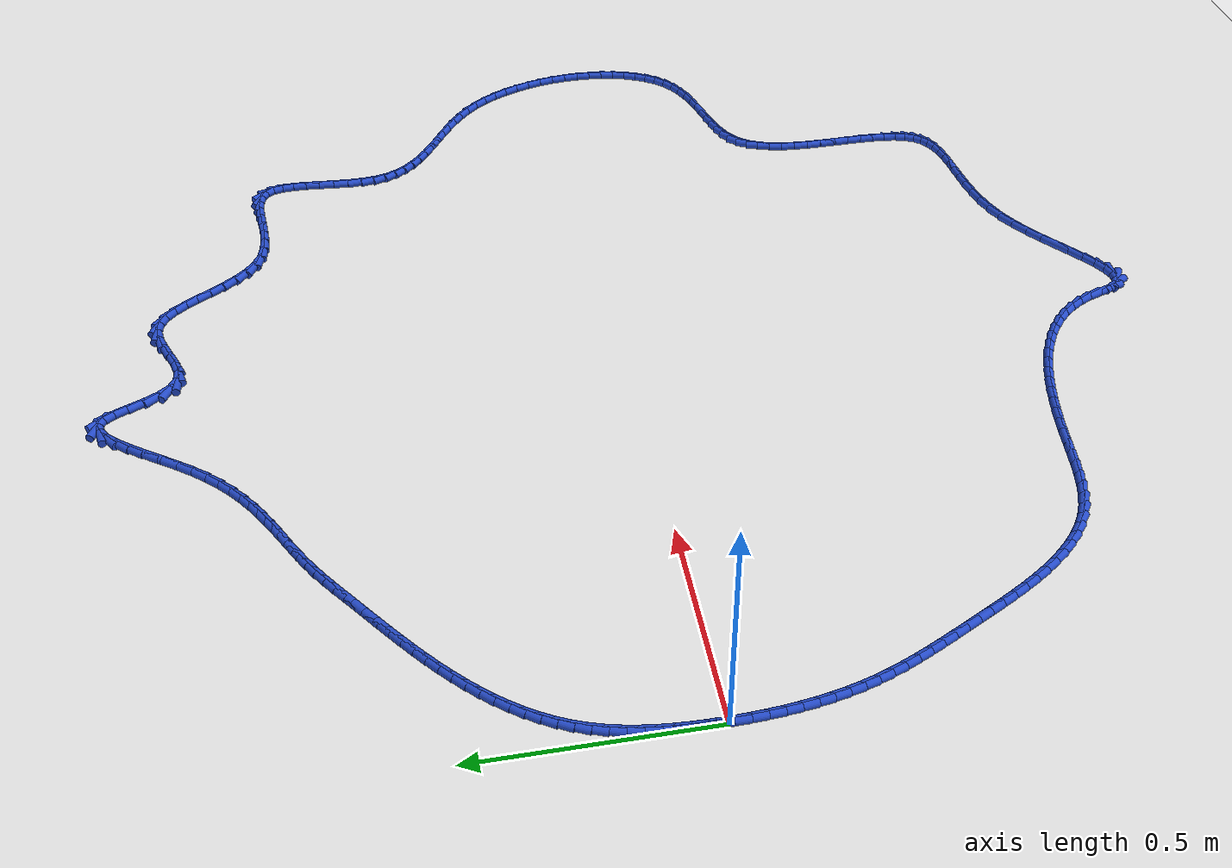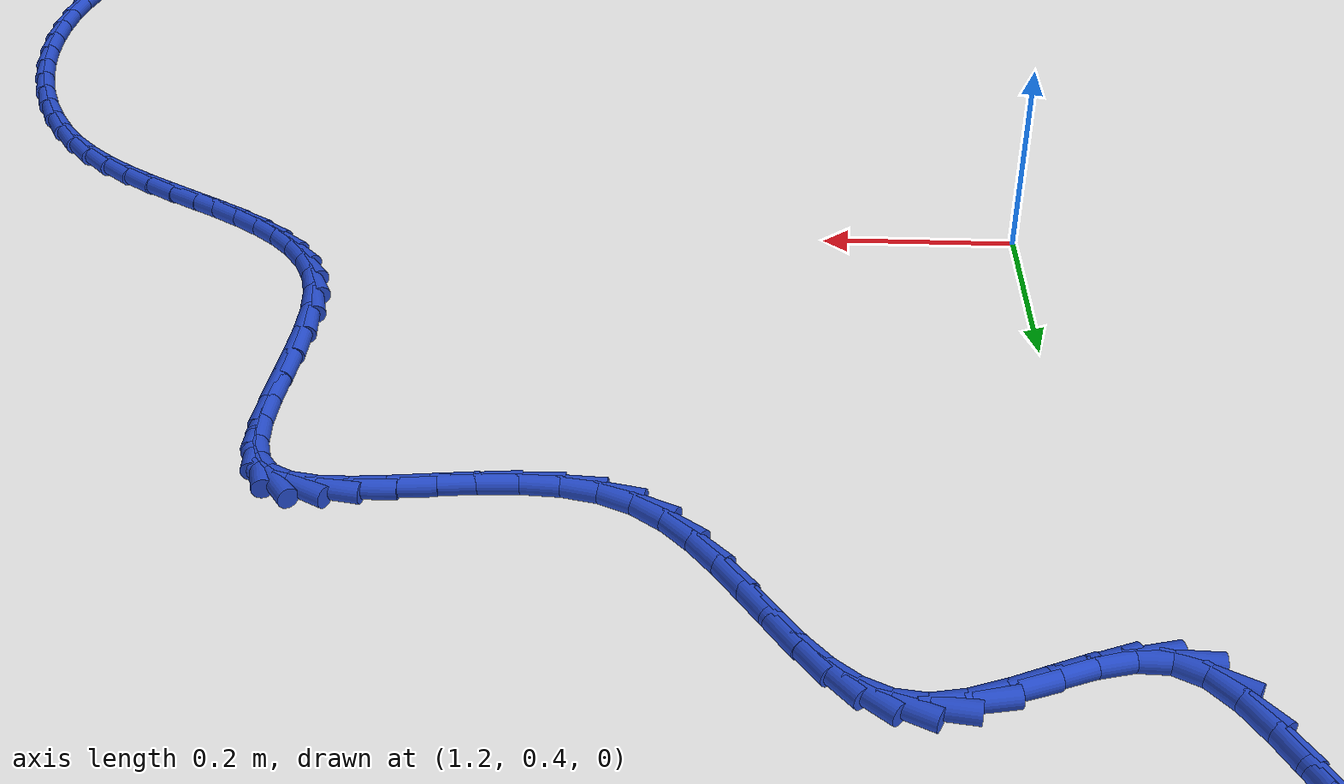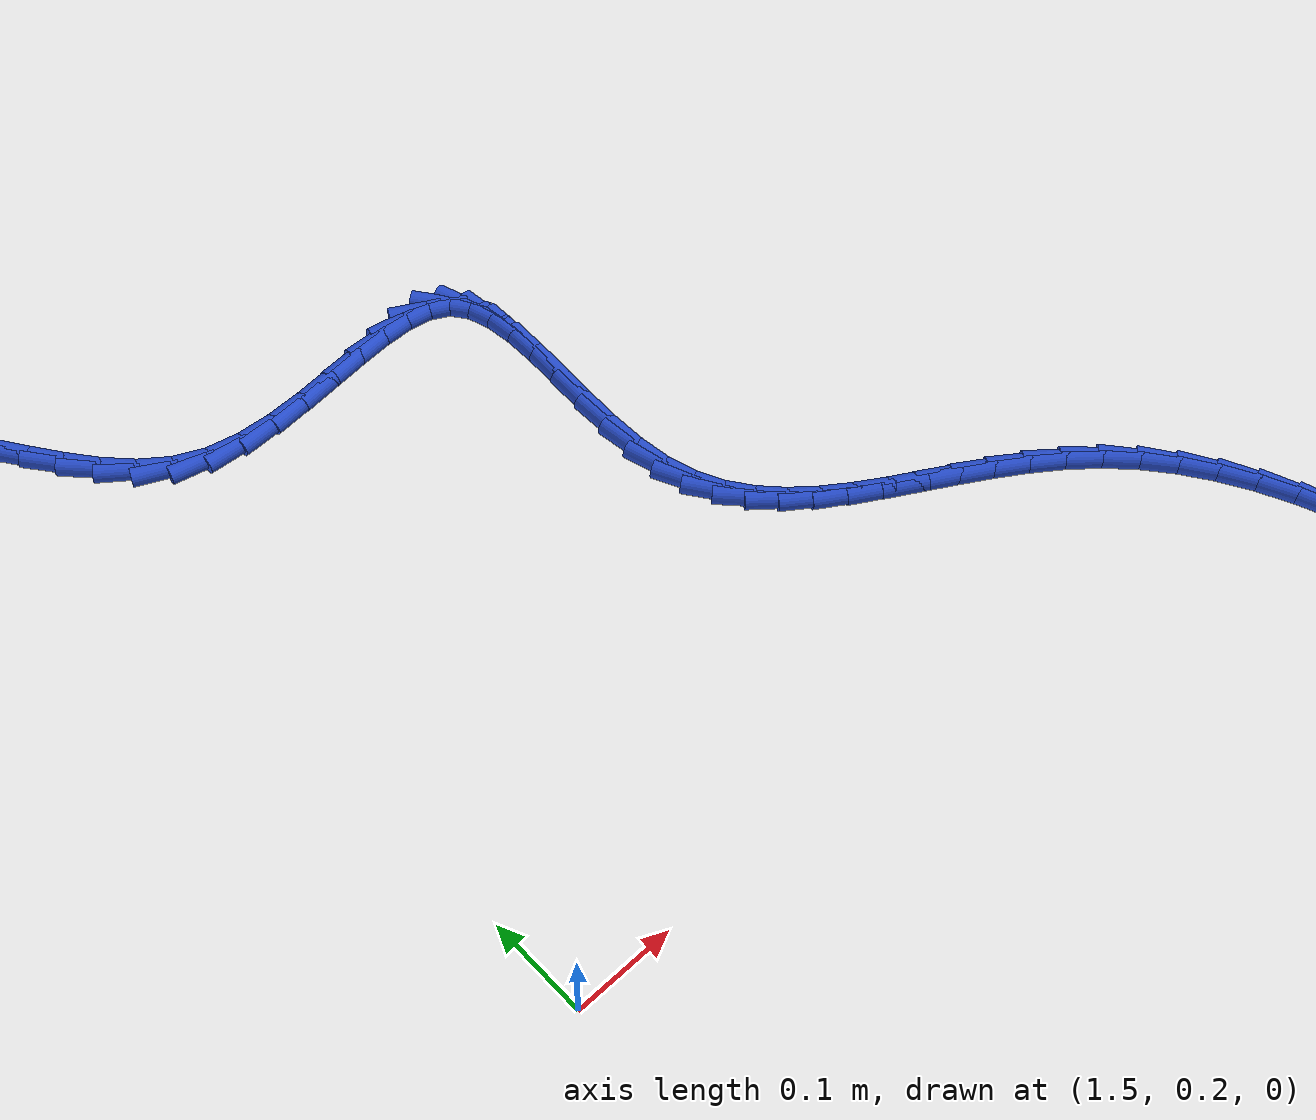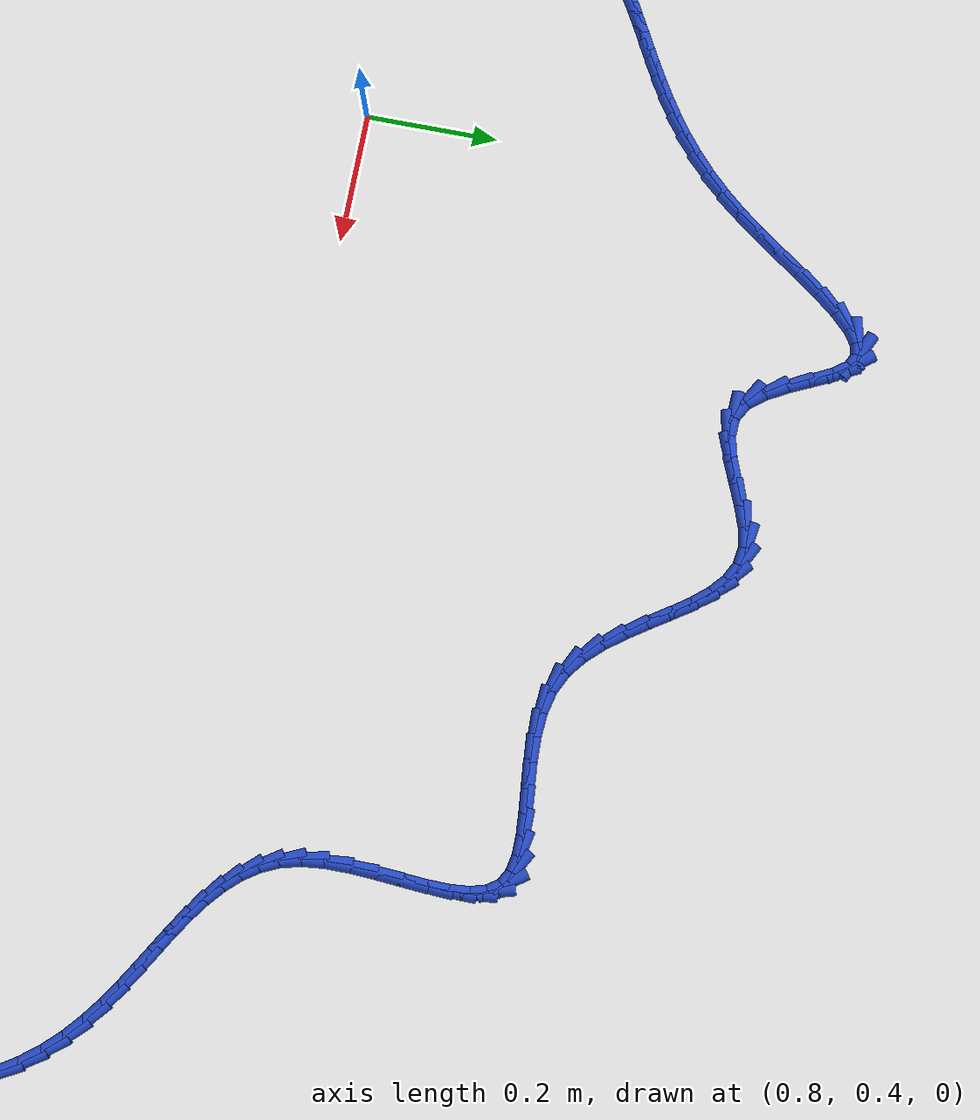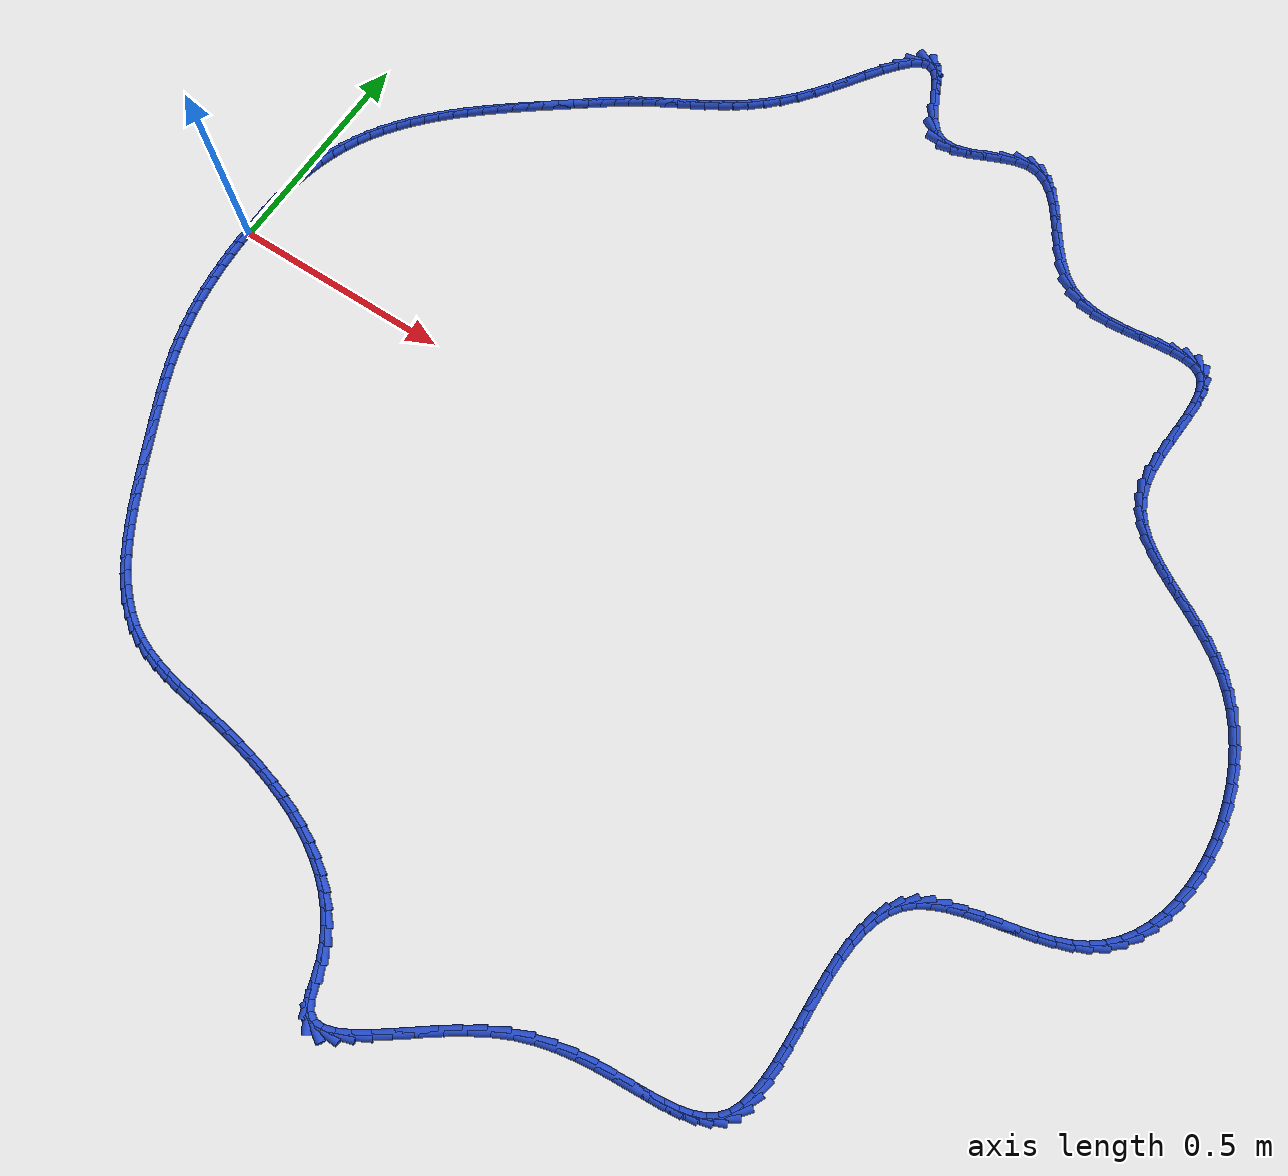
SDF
<sdf version="1.6">
 <world name="default">
  <light name="sun" type="directional">
   <pose>0 0 10 0 -0 0</pose>
   <diffuse>0.8 0.8 0.8 1</diffuse>
   <specular>0.2 0.2 0.2 1</specular>
   <attenuation>
    <range>1000</range>
    <constant>0.9</constant>
    <linear>0.01</linear>
    <quadratic>0.001</quadratic>
   </attenuation>
   <direction>-0.5 0.1 -0.9</direction>
  </light>
  <model name="ground_plane">
   <static>1</static>
   <link name="link">
    <collision name="collision">
     <geometry><plane><normal>0 0 1</normal><size>100 100</size></plane></geometry>
     <surface><friction><ode><mu>100</mu><mu2>50</mu2></ode></friction></surface>
    </collision>
    <visual name="visual">
     <cast_shadows>0</cast_shadows>
     <geometry><plane><normal>0 0 1</normal><size>100 100</size></plane></geometry>
     <material>
      <script><uri>file://media/materials/scripts/gazebo.material</uri><name>Gazebo/WhiteGlow</name></script>
     </material>
    </visual>
   </link>
  </model>
  <gravity>0 0 -9.8</gravity>
  <magnetic_field>6e-06 2.3e-05 -4.2e-05</magnetic_field>
  <atmosphere type="adiabatic"/>
  <physics name="default_physics" default="0" type="ode">
   <max_step_size>0.001</max_step_size>
   <real_time_factor>1</real_time_factor>
   <real_time_update_rate>1000</real_time_update_rate>
  </physics>
  <scene><ambient>0.4 0.4 0.4 1</ambient><background>0.7 0.7 0.7 1</background><shadows>1</shadows></scene>
  <spherical_coordinates>
   <surface_model>EARTH_WGS84</surface_model>
   <latitude_deg>0</latitude_deg>
   <longitude_deg>0</longitude_deg>
   <elevation>0</elevation>
   <heading_deg>0</heading_deg>
  </spherical_coordinates>
  <model name="line">
   <link name="link_0">
    <pose>-1.2576745200831851e-17 -1.3877787807814457e-17 0.01 0 1.57 -1.5650814311013574</pose>
    <collision name="collision">
     <geometry><cylinder><radius>0.01</radius><length>0.08</length></cylinder></geometry>
    </collision>
    <visual name="visual">
     <material>
      <script><name>Gazebo/Blue</name><uri>file://media/materials/scripts/gazebo.material</uri></script>
     </material>
     <geometry><cylinder><radius>0.01</radius><length>0.08</length></cylinder></geometry>
    </visual>
   </link>
   <link name="link_1">
    <pose>-0.00018875704975839807 0.03302859840996887 0.01 0 1.57 1.5498820778139464</pose>
    <collision name="collision">
     <geometry><cylinder><radius>0.01</radius><length>0.08</length></cylinder></geometry>
    </collision>
    <visual name="visual">
     <material>
      <script><name>Gazebo/Blue</name><uri>file://media/materials/scripts/gazebo.material</uri></script>
     </material>
     <geometry><cylinder><radius>0.01</radius><length>0.08</length></cylinder></geometry>
    </visual>
   </link>
   <link name="link_2">
    <pose>0.0005019491045792355 0.06604940856360342 0.01 0 1.57 1.5181562055893476</pose>
    <collision name="collision">
     <geometry><cylinder><radius>0.01</radius><length>0.08</length></cylinder></geometry>
    </collision>
    <visual name="visual">
     <material>
      <script><name>Gazebo/Blue</name><uri>file://media/materials/scripts/gazebo.material</uri></script>
     </material>
     <geometry><cylinder><radius>0.01</radius><length>0.08</length></cylinder></geometry>
    </visual>
   </link>
   <link name="link_3">
    <pose>0.0022342758914280373 0.09892787406148792 0.01 0 1.57 1.48097839300382</pose>
    <collision name="collision">
     <geometry><cylinder><radius>0.01</radius><length>0.08</length></cylinder></geometry>
    </collision>
    <visual name="visual">
     <material>
      <script><name>Gazebo/Blue</name><uri>file://media/materials/scripts/gazebo.material</uri></script>
     </material>
     <geometry><cylinder><radius>0.01</radius><length>0.08</length></cylinder></geometry>
    </visual>
   </link>
   <link name="link_4">
    <pose>0.005170380739203151 0.1315294385042066 0.01 0 1.57 1.437938783030213</pose>
    <collision name="collision">
     <geometry><cylinder><radius>0.01</radius><length>0.08</length></cylinder></geometry>
    </collision>
    <visual name="visual">
     <material>
      <script><name>Gazebo/Blue</name><uri>file://media/materials/scripts/gazebo.material</uri></script>
     </material>
     <geometry><cylinder><radius>0.01</radius><length>0.08</length></cylinder></geometry>
    </visual>
   </link>
   <link name="link_5">
    <pose>0.009472421076319728 0.16371954549234355 0.01 0 1.57 1.3885987296315616</pose>
    <collision name="collision">
     <geometry><cylinder><radius>0.01</radius><length>0.08</length></cylinder></geometry>
    </collision>
    <visual name="visual">
     <material>
      <script><name>Gazebo/Blue</name><uri>file://media/materials/scripts/gazebo.material</uri></script>
     </material>
     <geometry><cylinder><radius>0.01</radius><length>0.08</length></cylinder></geometry>
    </visual>
   </link>
   <link name="link_6">
    <pose>0.015302554331192916 0.19536363862648312 0.01 0 1.57 1.332531108004683</pose>
    <collision name="collision">
     <geometry><cylinder><radius>0.01</radius><length>0.08</length></cylinder></geometry>
    </collision>
    <visual name="visual">
     <material>
      <script><name>Gazebo/Blue</name><uri>file://media/materials/scripts/gazebo.material</uri></script>
     </material>
     <geometry><cylinder><radius>0.01</radius><length>0.08</length></cylinder></geometry>
    </visual>
   </link>
   <link name="link_7">
    <pose>0.022822937932237854 0.22632716150720936 0.01 0 1.57 1.2693802080843595</pose>
    <collision name="collision">
     <geometry><cylinder><radius>0.01</radius><length>0.08</length></cylinder></geometry>
    </collision>
    <visual name="visual">
     <material>
      <script><name>Gazebo/Blue</name><uri>file://media/materials/scripts/gazebo.material</uri></script>
     </material>
     <geometry><cylinder><radius>0.01</radius><length>0.08</length></cylinder></geometry>
    </visual>
   </link>
   <link name="link_8">
    <pose>0.032195729307869694 0.25647555773510666 0.01 0 1.57 1.1992514912946248</pose>
    <collision name="collision">
     <geometry><cylinder><radius>0.01</radius><length>0.08</length></cylinder></geometry>
    </collision>
    <visual name="visual">
     <material>
      <script><name>Gazebo/Blue</name><uri>file://media/materials/scripts/gazebo.material</uri></script>
     </material>
     <geometry><cylinder><radius>0.01</radius><length>0.08</length></cylinder></geometry>
    </visual>
   </link>
   <link name="link_9">
    <pose>0.04357478084958287 0.28567946065682875 0.01 0 1.57 1.1279907039054222</pose>
    <collision name="collision">
     <geometry><cylinder><radius>0.01</radius><length>0.08</length></cylinder></geometry>
    </collision>
    <visual name="visual">
     <material>
      <script><name>Gazebo/Blue</name><uri>file://media/materials/scripts/gazebo.material</uri></script>
     </material>
     <geometry><cylinder><radius>0.01</radius><length>0.08</length></cylinder></geometry>
    </visual>
   </link>
   <link name="link_10">
    <pose>0.05696001385919434 0.31390569383169914 0.01 0 1.57 1.0612166555067772</pose>
    <collision name="collision">
     <geometry><cylinder><radius>0.01</radius><length>0.08</length></cylinder></geometry>
    </collision>
    <visual name="visual">
     <material>
      <script><name>Gazebo/Blue</name><uri>file://media/materials/scripts/gazebo.material</uri></script>
     </material>
     <geometry><cylinder><radius>0.01</radius><length>0.08</length></cylinder></geometry>
    </visual>
   </link>
   <link name="link_11">
    <pose>0.072215574518545 0.34120592552255874 0.01 0 1.57 0.9995811922866852</pose>
    <collision name="collision">
     <geometry><cylinder><radius>0.01</radius><length>0.08</length></cylinder></geometry>
    </collision>
    <visual name="visual">
     <material>
      <script><name>Gazebo/Blue</name><uri>file://media/materials/scripts/gazebo.material</uri></script>
     </material>
     <geometry><cylinder><radius>0.01</radius><length>0.08</length></cylinder></geometry>
    </visual>
   </link>
   <link name="link_12">
    <pose>0.08920095310589866 0.367634733426309 0.01 0 1.57 0.9433342273357663</pose>
    <collision name="collision">
     <geometry><cylinder><radius>0.01</radius><length>0.08</length></cylinder></geometry>
    </collision>
    <visual name="visual">
     <material>
      <script><name>Gazebo/Blue</name><uri>file://media/materials/scripts/gazebo.material</uri></script>
     </material>
     <geometry><cylinder><radius>0.01</radius><length>0.08</length></cylinder></geometry>
    </visual>
   </link>
   <link name="link_13">
    <pose>0.10777563989951901 0.39324669523985106 0.01 0 1.57 0.8925384946941762</pose>
    <collision name="collision">
     <geometry><cylinder><radius>0.01</radius><length>0.08</length></cylinder></geometry>
    </collision>
    <visual name="visual">
     <material>
      <script><name>Gazebo/Blue</name><uri>file://media/materials/scripts/gazebo.material</uri></script>
     </material>
     <geometry><cylinder><radius>0.01</radius><length>0.08</length></cylinder></geometry>
    </visual>
   </link>
   <link name="link_14">
    <pose>0.1277991251776699 0.4180963886600861 0.01 0 1.57 0.84711855570302</pose>
    <collision name="collision">
     <geometry><cylinder><radius>0.01</radius><length>0.08</length></cylinder></geometry>
    </collision>
    <visual name="visual">
     <material>
      <script><name>Gazebo/Blue</name><uri>file://media/materials/scripts/gazebo.material</uri></script>
     </material>
     <geometry><cylinder><radius>0.01</radius><length>0.08</length></cylinder></geometry>
    </visual>
   </link>
   <link name="link_15">
    <pose>0.14913089921861505 0.4422383913839154 0.01 0 1.57 0.8069075688820014</pose>
    <collision name="collision">
     <geometry><cylinder><radius>0.01</radius><length>0.08</length></cylinder></geometry>
    </collision>
    <visual name="visual">
     <material>
      <script><name>Gazebo/Blue</name><uri>file://media/materials/scripts/gazebo.material</uri></script>
     </material>
     <geometry><cylinder><radius>0.01</radius><length>0.08</length></cylinder></geometry>
    </visual>
   </link>
   <link name="link_16">
    <pose>0.17163045230061832 0.4657272811082405 0.01 0 1.57 0.7716871163484621</pose>
    <collision name="collision">
     <geometry><cylinder><radius>0.01</radius><length>0.08</length></cylinder></geometry>
    </collision>
    <visual name="visual">
     <material>
      <script><name>Gazebo/Blue</name><uri>file://media/materials/scripts/gazebo.material</uri></script>
     </material>
     <geometry><cylinder><radius>0.01</radius><length>0.08</length></cylinder></geometry>
    </visual>
   </link>
   <link name="link_17">
    <pose>0.19515727470194344 0.4886176355299623 0.01 0 1.57 0.741218501211821</pose>
    <collision name="collision">
     <geometry><cylinder><radius>0.01</radius><length>0.08</length></cylinder></geometry>
    </collision>
    <visual name="visual">
     <material>
      <script><name>Gazebo/Blue</name><uri>file://media/materials/scripts/gazebo.material</uri></script>
     </material>
     <geometry><cylinder><radius>0.01</radius><length>0.08</length></cylinder></geometry>
    </visual>
   </link>
   <link name="link_18">
    <pose>0.21957085670085416 0.5109640323459822 0.01 0 1.57 0.7152658964969497</pose>
    <collision name="collision">
     <geometry><cylinder><radius>0.01</radius><length>0.08</length></cylinder></geometry>
    </collision>
    <visual name="visual">
     <material>
      <script><name>Gazebo/Blue</name><uri>file://media/materials/scripts/gazebo.material</uri></script>
     </material>
     <geometry><cylinder><radius>0.01</radius><length>0.08</length></cylinder></geometry>
    </visual>
   </link>
   <link name="link_19">
    <pose>0.2447306885756142 0.5328210492532011 0.01 0 1.57 0.6936126866799566</pose>
    <collision name="collision">
     <geometry><cylinder><radius>0.01</radius><length>0.08</length></cylinder></geometry>
    </collision>
    <visual name="visual">
     <material>
      <script><name>Gazebo/Blue</name><uri>file://media/materials/scripts/gazebo.material</uri></script>
     </material>
     <geometry><cylinder><radius>0.01</radius><length>0.08</length></cylinder></geometry>
    </visual>
   </link>
   <link name="link_20">
    <pose>0.2704962606044876 0.554243263948521 0.01 0 1.57 0.6760726265058145</pose>
    <collision name="collision">
     <geometry><cylinder><radius>0.01</radius><length>0.08</length></cylinder></geometry>
    </collision>
    <visual name="visual">
     <material>
      <script><name>Gazebo/Blue</name><uri>file://media/materials/scripts/gazebo.material</uri></script>
     </material>
     <geometry><cylinder><radius>0.01</radius><length>0.08</length></cylinder></geometry>
    </visual>
   </link>
   <link name="link_21">
    <pose>0.2967270630657379 0.5752852541288426 0.01 0 1.57 0.6624973541152003</pose>
    <collision name="collision">
     <geometry><cylinder><radius>0.01</radius><length>0.08</length></cylinder></geometry>
    </collision>
    <visual name="visual">
     <material>
      <script><name>Gazebo/Blue</name><uri>file://media/materials/scripts/gazebo.material</uri></script>
     </material>
     <geometry><cylinder><radius>0.01</radius><length>0.08</length></cylinder></geometry>
    </visual>
   </link>
   <link name="link_22">
    <pose>0.3232825862376289 0.5960015974910671 0.01 0 1.57 0.6527815501281055</pose>
    <collision name="collision">
     <geometry><cylinder><radius>0.01</radius><length>0.08</length></cylinder></geometry>
    </collision>
    <visual name="visual">
     <material>
      <script><name>Gazebo/Blue</name><uri>file://media/materials/scripts/gazebo.material</uri></script>
     </material>
     <geometry><cylinder><radius>0.01</radius><length>0.08</length></cylinder></geometry>
    </visual>
   </link>
   <link name="link_23">
    <pose>0.3500223203984246 0.6164468717320963 0.01 0 1.57 0.6468667538111215</pose>
    <collision name="collision">
     <geometry><cylinder><radius>0.01</radius><length>0.08</length></cylinder></geometry>
    </collision>
    <visual name="visual">
     <material>
      <script><name>Gazebo/Blue</name><uri>file://media/materials/scripts/gazebo.material</uri></script>
     </material>
     <geometry><cylinder><radius>0.01</radius><length>0.08</length></cylinder></geometry>
    </visual>
   </link>
   <link name="link_24">
    <pose>0.3768057558263884 0.6366756545488307 0.01 0 1.57 0.6447445883824877</pose>
    <collision name="collision">
     <geometry><cylinder><radius>0.01</radius><length>0.08</length></cylinder></geometry>
    </collision>
    <visual name="visual">
     <material>
      <script><name>Gazebo/Blue</name><uri>file://media/materials/scripts/gazebo.material</uri></script>
     </material>
     <geometry><cylinder><radius>0.01</radius><length>0.08</length></cylinder></geometry>
    </visual>
   </link>
   <link name="link_25">
    <pose>0.40349238279978406 0.6567425236381718 0.01 0 1.57 0.6462652594409077</pose>
    <collision name="collision">
     <geometry><cylinder><radius>0.01</radius><length>0.08</length></cylinder></geometry>
    </collision>
    <visual name="visual">
     <material>
      <script><name>Gazebo/Blue</name><uri>file://media/materials/scripts/gazebo.material</uri></script>
     </material>
     <geometry><cylinder><radius>0.01</radius><length>0.08</length></cylinder></geometry>
    </visual>
   </link>
   <link name="link_26">
    <pose>0.42994488042396417 0.6766963824401204 0.01 0 1.57 0.6450878106839766</pose>
    <collision name="collision">
     <geometry><cylinder><radius>0.01</radius><length>0.08</length></cylinder></geometry>
    </collision>
    <visual name="visual">
     <material>
      <script><name>Gazebo/Blue</name><uri>file://media/materials/scripts/gazebo.material</uri></script>
     </material>
     <geometry><cylinder><radius>0.01</radius><length>0.08</length></cylinder></geometry>
    </visual>
   </link>
   <link name="link_27">
    <pose>0.45613028760877433 0.6964004346610475 0.01 0 1.57 0.6332548885754912</pose>
    <collision name="collision">
     <geometry><cylinder><radius>0.01</radius><length>0.08</length></cylinder></geometry>
    </collision>
    <visual name="visual">
     <material>
      <script><name>Gazebo/Blue</name><uri>file://media/materials/scripts/gazebo.material</uri></script>
     </material>
     <geometry><cylinder><radius>0.01</radius><length>0.08</length></cylinder></geometry>
    </visual>
   </link>
   <link name="link_28">
    <pose>0.48214084717580136 0.7154950938902668 0.01 0 1.57 0.609632096276374</pose>
    <collision name="collision">
     <geometry><cylinder><radius>0.01</radius><length>0.08</length></cylinder></geometry>
    </collision>
    <visual name="visual">
     <material>
      <script><name>Gazebo/Blue</name><uri>file://media/materials/scripts/gazebo.material</uri></script>
     </material>
     <geometry><cylinder><radius>0.01</radius><length>0.08</length></cylinder></geometry>
    </visual>
   </link>
   <link name="link_29">
    <pose>0.5080762029777084 0.7336076041878276 0.01 0 1.57 0.5744436096678182</pose>
    <collision name="collision">
     <geometry><cylinder><radius>0.01</radius><length>0.08</length></cylinder></geometry>
    </collision>
    <visual name="visual">
     <material>
      <script><name>Gazebo/Blue</name><uri>file://media/materials/scripts/gazebo.material</uri></script>
     </material>
     <geometry><cylinder><radius>0.01</radius><length>0.08</length></cylinder></geometry>
    </visual>
   </link>
   <link name="link_30">
    <pose>0.5340301528876847 0.7504064468693635 0.01 0 1.57 0.540824603150551</pose>
    <collision name="collision">
     <geometry><cylinder><radius>0.01</radius><length>0.08</length></cylinder></geometry>
    </collision>
    <visual name="visual">
     <material>
      <script><name>Gazebo/Blue</name><uri>file://media/materials/scripts/gazebo.material</uri></script>
     </material>
     <geometry><cylinder><radius>0.01</radius><length>0.08</length></cylinder></geometry>
    </visual>
   </link>
   <link name="link_31">
    <pose>0.5600311066978237 0.7660213476022555 0.01 0 1.57 0.518349899339467</pose>
    <collision name="collision">
     <geometry><cylinder><radius>0.01</radius><length>0.08</length></cylinder></geometry>
    </collision>
    <visual name="visual">
     <material>
      <script><name>Gazebo/Blue</name><uri>file://media/materials/scripts/gazebo.material</uri></script>
     </material>
     <geometry><cylinder><radius>0.01</radius><length>0.08</length></cylinder></geometry>
    </visual>
   </link>
   <link name="link_32">
    <pose>0.5860664781020841 0.780871216541192 0.01 0 1.57 0.5080461604106687</pose>
    <collision name="collision">
     <geometry><cylinder><radius>0.01</radius><length>0.08</length></cylinder></geometry>
    </collision>
    <visual name="visual">
     <material>
      <script><name>Gazebo/Blue</name><uri>file://media/materials/scripts/gazebo.material</uri></script>
     </material>
     <geometry><cylinder><radius>0.01</radius><length>0.08</length></cylinder></geometry>
    </visual>
   </link>
   <link name="link_33">
    <pose>0.6121230490440451 0.7953794201773916 0.01 0 1.57 0.5103059193853607</pose>
    <collision name="collision">
     <geometry><cylinder><radius>0.01</radius><length>0.08</length></cylinder></geometry>
    </collision>
    <visual name="visual">
     <material>
      <script><name>Gazebo/Blue</name><uri>file://media/materials/scripts/gazebo.material</uri></script>
     </material>
     <geometry><cylinder><radius>0.01</radius><length>0.08</length></cylinder></geometry>
    </visual>
   </link>
   <link name="link_34">
    <pose>0.6381876014672856 0.8099693250020739 0.01 0 1.57 0.5250256714655829</pose>
    <collision name="collision">
     <geometry><cylinder><radius>0.01</radius><length>0.08</length></cylinder></geometry>
    </collision>
    <visual name="visual">
     <material>
      <script><name>Gazebo/Blue</name><uri>file://media/materials/scripts/gazebo.material</uri></script>
     </material>
     <geometry><cylinder><radius>0.01</radius><length>0.08</length></cylinder></geometry>
    </visual>
   </link>
   <link name="link_35">
    <pose>0.6642469173153848 0.8250642975064575 0.01 0 1.57 0.5516065530024408</pose>
    <collision name="collision">
     <geometry><cylinder><radius>0.01</radius><length>0.08</length></cylinder></geometry>
    </collision>
    <visual name="visual">
     <material>
      <script><name>Gazebo/Blue</name><uri>file://media/materials/scripts/gazebo.material</uri></script>
     </material>
     <geometry><cylinder><radius>0.01</radius><length>0.08</length></cylinder></geometry>
    </visual>
   </link>
   <link name="link_36">
    <pose>0.6902877785319216 0.8410877041817618 0.01 0 1.57 0.5889535420432759</pose>
    <collision name="collision">
     <geometry><cylinder><radius>0.01</radius><length>0.08</length></cylinder></geometry>
    </collision>
    <visual name="visual">
     <material>
      <script><name>Gazebo/Blue</name><uri>file://media/materials/scripts/gazebo.material</uri></script>
     </material>
     <geometry><cylinder><radius>0.01</radius><length>0.08</length></cylinder></geometry>
    </visual>
   </link>
   <link name="link_37">
    <pose>0.716296967060475 0.8584629115192056 0.01 0 1.57 0.6354955214558552</pose>
    <collision name="collision">
     <geometry><cylinder><radius>0.01</radius><length>0.08</length></cylinder></geometry>
    </collision>
    <visual name="visual">
     <material>
      <script><name>Gazebo/Blue</name><uri>file://media/materials/scripts/gazebo.material</uri></script>
     </material>
     <geometry><cylinder><radius>0.01</radius><length>0.08</length></cylinder></geometry>
    </visual>
   </link>
   <link name="link_38">
    <pose>0.742261264844624 0.8776132860100079 0.01 0 1.57 0.6892555066532088</pose>
    <collision name="collision">
     <geometry><cylinder><radius>0.01</radius><length>0.08</length></cylinder></geometry>
    </collision>
    <visual name="visual">
     <material>
      <script><name>Gazebo/Blue</name><uri>file://media/materials/scripts/gazebo.material</uri></script>
     </material>
     <geometry><cylinder><radius>0.01</radius><length>0.08</length></cylinder></geometry>
    </visual>
   </link>
   <link name="link_39">
    <pose>0.7681674538279477 0.8989621941453881 0.01 0 1.57 0.7479890849613909</pose>
    <collision name="collision">
     <geometry><cylinder><radius>0.01</radius><length>0.08</length></cylinder></geometry>
    </collision>
    <visual name="visual">
     <material>
      <script><name>Gazebo/Blue</name><uri>file://media/materials/scripts/gazebo.material</uri></script>
     </material>
     <geometry><cylinder><radius>0.01</radius><length>0.08</length></cylinder></geometry>
    </visual>
   </link>
   <link name="link_40">
    <pose>0.7940023159540255 0.9229330024165652 0.01 0 1.57 0.809381516008995</pose>
    <collision name="collision">
     <geometry><cylinder><radius>0.01</radius><length>0.08</length></cylinder></geometry>
    </collision>
    <visual name="visual">
     <material>
      <script><name>Gazebo/Blue</name><uri>file://media/materials/scripts/gazebo.material</uri></script>
     </material>
     <geometry><cylinder><radius>0.01</radius><length>0.08</length></cylinder></geometry>
    </visual>
   </link>
   <link name="link_41">
    <pose>0.8197526331664358 0.9499490773147576 0.01 0 1.57 0.8712639860786564</pose>
    <collision name="collision">
     <geometry><cylinder><radius>0.01</radius><length>0.08</length></cylinder></geometry>
    </collision>
    <visual name="visual">
     <material>
      <script><name>Gazebo/Blue</name><uri>file://media/materials/scripts/gazebo.material</uri></script>
     </material>
     <geometry><cylinder><radius>0.01</radius><length>0.08</length></cylinder></geometry>
    </visual>
   </link>
   <link name="link_42">
    <pose>0.8454051874087583 0.9804337853311855 0.01 0 1.57 0.9275647869740576</pose>
    <collision name="collision">
     <geometry><cylinder><radius>0.01</radius><length>0.08</length></cylinder></geometry>
    </collision>
    <visual name="visual">
     <material>
      <script><name>Gazebo/Blue</name><uri>file://media/materials/scripts/gazebo.material</uri></script>
     </material>
     <geometry><cylinder><radius>0.01</radius><length>0.08</length></cylinder></geometry>
    </visual>
   </link>
   <link name="link_43">
    <pose>0.8709216324254584 1.014474825673467 0.01 0 1.57 0.9600698403931758</pose>
    <collision name="collision">
     <geometry><cylinder><radius>0.01</radius><length>0.08</length></cylinder></geometry>
    </collision>
    <visual name="visual">
     <material>
      <script><name>Gazebo/Blue</name><uri>file://media/materials/scripts/gazebo.material</uri></script>
     </material>
     <geometry><cylinder><radius>0.01</radius><length>0.08</length></cylinder></geometry>
    </visual>
   </link>
   <link name="link_44">
    <pose>0.896139370747404 1.0505001261041893 0.01 0 1.57 0.9681425664664552</pose>
    <collision name="collision">
     <geometry><cylinder><radius>0.01</radius><length>0.08</length></cylinder></geometry>
    </collision>
    <visual name="visual">
     <material>
      <script><name>Gazebo/Blue</name><uri>file://media/materials/scripts/gazebo.material</uri></script>
     </material>
     <geometry><cylinder><radius>0.01</radius><length>0.08</length></cylinder></geometry>
    </visual>
   </link>
   <link name="link_45">
    <pose>0.9208574692893257 1.0864255199029347 0.01 0 1.57 0.9521839637314978</pose>
    <collision name="collision">
     <geometry><cylinder><radius>0.01</radius><length>0.08</length></cylinder></geometry>
    </collision>
    <visual name="visual">
     <material>
      <script><name>Gazebo/Blue</name><uri>file://media/materials/scripts/gazebo.material</uri></script>
     </material>
     <geometry><cylinder><radius>0.01</radius><length>0.08</length></cylinder></geometry>
    </visual>
   </link>
   <link name="link_46">
    <pose>0.944874984016002 1.120166694077723 0.01 0 1.57 0.9056896578907303</pose>
    <collision name="collision">
     <geometry><cylinder><radius>0.01</radius><length>0.08</length></cylinder></geometry>
    </collision>
    <visual name="visual">
     <material>
      <script><name>Gazebo/Blue</name><uri>file://media/materials/scripts/gazebo.material</uri></script>
     </material>
     <geometry><cylinder><radius>0.01</radius><length>0.08</length></cylinder></geometry>
    </visual>
   </link>
   <link name="link_47">
    <pose>0.9679909708922108 1.1496393356365728 0.01 0 1.57 0.8099046634219983</pose>
    <collision name="collision">
     <geometry><cylinder><radius>0.01</radius><length>0.08</length></cylinder></geometry>
    </collision>
    <visual name="visual">
     <material>
      <script><name>Gazebo/Blue</name><uri>file://media/materials/scripts/gazebo.material</uri></script>
     </material>
     <geometry><cylinder><radius>0.01</radius><length>0.08</length></cylinder></geometry>
    </visual>
   </link>
   <link name="link_48">
    <pose>0.9900044858827304 1.172759131587503 0.01 0 1.57 0.6167142860689221</pose>
    <collision name="collision">
     <geometry><cylinder><radius>0.01</radius><length>0.08</length></cylinder></geometry>
    </collision>
    <visual name="visual">
     <material>
      <script><name>Gazebo/Blue</name><uri>file://media/materials/scripts/gazebo.material</uri></script>
     </material>
     <geometry><cylinder><radius>0.01</radius><length>0.08</length></cylinder></geometry>
    </visual>
   </link>
   <link name="link_49">
    <pose>1.0107145849523387 1.1874417689385328 0.01 0 1.57 0.21336477712065735</pose>
    <collision name="collision">
     <geometry><cylinder><radius>0.01</radius><length>0.08</length></cylinder></geometry>
    </collision>
    <visual name="visual">
     <material>
      <script><name>Gazebo/Blue</name><uri>file://media/materials/scripts/gazebo.material</uri></script>
     </material>
     <geometry><cylinder><radius>0.01</radius><length>0.08</length></cylinder></geometry>
    </visual>
   </link>
   <link name="link_50">
    <pose>1.029920324065814 1.1916029346976815 0.01 0 1.57 -0.4494004433744486</pose>
    <collision name="collision">
     <geometry><cylinder><radius>0.01</radius><length>0.08</length></cylinder></geometry>
    </collision>
    <visual name="visual">
     <material>
      <script><name>Gazebo/Blue</name><uri>file://media/materials/scripts/gazebo.material</uri></script>
     </material>
     <geometry><cylinder><radius>0.01</radius><length>0.08</length></cylinder></geometry>
    </visual>
   </link>
   <link name="link_51">
    <pose>1.0474214323632418 1.1831618732783176 0.01 0 1.57 -0.9298503274344448</pose>
    <collision name="collision">
     <geometry><cylinder><radius>0.01</radius><length>0.08</length></cylinder></geometry>
    </collision>
    <visual name="visual">
     <material>
      <script><name>Gazebo/Blue</name><uri>file://media/materials/scripts/gazebo.material</uri></script>
     </material>
     <geometry><cylinder><radius>0.01</radius><length>0.08</length></cylinder></geometry>
    </visual>
   </link>
   <link name="link_52">
    <pose>1.0633524372819556 1.161807075886515 0.01 0 1.57 -1.0966642260439485</pose>
    <collision name="collision">
     <geometry><cylinder><radius>0.01</radius><length>0.08</length></cylinder></geometry>
    </collision>
    <visual name="visual">
     <material>
      <script><name>Gazebo/Blue</name><uri>file://media/materials/scripts/gazebo.material</uri></script>
     </material>
     <geometry><cylinder><radius>0.01</radius><length>0.08</length></cylinder></geometry>
    </visual>
   </link>
   <link name="link_53">
    <pose>1.0787234840074886 1.1318542492947743 0.01 0 1.57 -1.1259893347179983</pose>
    <collision name="collision">
     <geometry><cylinder><radius>0.01</radius><length>0.08</length></cylinder></geometry>
    </collision>
    <visual name="visual">
     <material>
      <script><name>Gazebo/Blue</name><uri>file://media/materials/scripts/gazebo.material</uri></script>
     </material>
     <geometry><cylinder><radius>0.01</radius><length>0.08</length></cylinder></geometry>
    </visual>
   </link>
   <link name="link_54">
    <pose>1.0946860972045622 1.098366222325393 0.01 0 1.57 -1.0648958203347527</pose>
    <collision name="collision">
     <geometry><cylinder><radius>0.01</radius><length>0.08</length></cylinder></geometry>
    </collision>
    <visual name="visual">
     <material>
      <script><name>Gazebo/Blue</name><uri>file://media/materials/scripts/gazebo.material</uri></script>
     </material>
     <geometry><cylinder><radius>0.01</radius><length>0.08</length></cylinder></geometry>
    </visual>
   </link>
   <link name="link_55">
    <pose>1.1123918015378984 1.0664058238006695 0.01 0 1.57 -0.8887827363853509</pose>
    <collision name="collision">
     <geometry><cylinder><radius>0.01</radius><length>0.08</length></cylinder></geometry>
    </collision>
    <visual name="visual">
     <material>
      <script><name>Gazebo/Blue</name><uri>file://media/materials/scripts/gazebo.material</uri></script>
     </material>
     <geometry><cylinder><radius>0.01</radius><length>0.08</length></cylinder></geometry>
    </visual>
   </link>
   <link name="link_56">
    <pose>1.1329921216722192 1.0410358825429014 0.01 0 1.57 -0.5116753596276041</pose>
    <collision name="collision">
     <geometry><cylinder><radius>0.01</radius><length>0.08</length></cylinder></geometry>
    </collision>
    <visual name="visual">
     <material>
      <script><name>Gazebo/Blue</name><uri>file://media/materials/scripts/gazebo.material</uri></script>
     </material>
     <geometry><cylinder><radius>0.01</radius><length>0.08</length></cylinder></geometry>
    </visual>
   </link>
   <link name="link_57">
    <pose>1.1576093824203002 1.027211805456631 0.01 0 1.57 -0.03925318195446498</pose>
    <collision name="collision">
     <geometry><cylinder><radius>0.01</radius><length>0.08</length></cylinder></geometry>
    </collision>
    <visual name="visual">
     <material>
      <script><name>Gazebo/Blue</name><uri>file://media/materials/scripts/gazebo.material</uri></script>
     </material>
     <geometry><cylinder><radius>0.01</radius><length>0.08</length></cylinder></geometry>
    </visual>
   </link>
   <link name="link_58">
    <pose>1.1863315612279193 1.02608378913244 0.01 0 1.57 0.2471443779884811</pose>
    <collision name="collision">
     <geometry><cylinder><radius>0.01</radius><length>0.08</length></cylinder></geometry>
    </collision>
    <visual name="visual">
     <material>
      <script><name>Gazebo/Blue</name><uri>file://media/materials/scripts/gazebo.material</uri></script>
     </material>
     <geometry><cylinder><radius>0.01</radius><length>0.08</length></cylinder></geometry>
    </visual>
   </link>
   <link name="link_59">
    <pose>1.2179585491378866 1.0340633516257896 0.01 0 1.57 0.37794571140664307</pose>
    <collision name="collision">
     <geometry><cylinder><radius>0.01</radius><length>0.08</length></cylinder></geometry>
    </collision>
    <visual name="visual">
     <material>
      <script><name>Gazebo/Blue</name><uri>file://media/materials/scripts/gazebo.material</uri></script>
     </material>
     <geometry><cylinder><radius>0.01</radius><length>0.08</length></cylinder></geometry>
    </visual>
   </link>
   <link name="link_60">
    <pose>1.251209522628642 1.0472650740997405 0.01 0 1.57 0.4084316908271969</pose>
    <collision name="collision">
     <geometry><cylinder><radius>0.01</radius><length>0.08</length></cylinder></geometry>
    </collision>
    <visual name="visual">
     <material>
      <script><name>Gazebo/Blue</name><uri>file://media/materials/scripts/gazebo.material</uri></script>
     </material>
     <geometry><cylinder><radius>0.01</radius><length>0.08</length></cylinder></geometry>
    </visual>
   </link>
   <link name="link_61">
    <pose>1.2848036581786273 1.0618035377173545 0.01 0 1.57 0.3518697404255531</pose>
    <collision name="collision">
     <geometry><cylinder><radius>0.01</radius><length>0.08</length></cylinder></geometry>
    </collision>
    <visual name="visual">
     <material>
      <script><name>Gazebo/Blue</name><uri>file://media/materials/scripts/gazebo.material</uri></script>
     </material>
     <geometry><cylinder><radius>0.01</radius><length>0.08</length></cylinder></geometry>
    </visual>
   </link>
   <link name="link_62">
    <pose>1.3174601322662831 1.073793323641692 0.01 0 1.57 0.1805374693753123</pose>
    <collision name="collision">
     <geometry><cylinder><radius>0.01</radius><length>0.08</length></cylinder></geometry>
    </collision>
    <visual name="visual">
     <material>
      <script><name>Gazebo/Blue</name><uri>file://media/materials/scripts/gazebo.material</uri></script>
     </material>
     <geometry><cylinder><radius>0.01</radius><length>0.08</length></cylinder></geometry>
    </visual>
   </link>
   <link name="link_63">
    <pose>1.347898121370051 1.079349013035815 0.01 0 1.57 -0.1399753026989773</pose>
    <collision name="collision">
     <geometry><cylinder><radius>0.01</radius><length>0.08</length></cylinder></geometry>
    </collision>
    <visual name="visual">
     <material>
      <script><name>Gazebo/Blue</name><uri>file://media/materials/scripts/gazebo.material</uri></script>
     </material>
     <geometry><cylinder><radius>0.01</radius><length>0.08</length></cylinder></geometry>
    </visual>
   </link>
   <link name="link_64">
    <pose>1.3751642141030875 1.0755073103481927 0.01 0 1.57 -0.47209147640019355</pose>
    <collision name="collision">
     <geometry><cylinder><radius>0.01</radius><length>0.08</length></cylinder></geometry>
    </collision>
    <visual name="visual">
     <material>
      <script><name>Gazebo/Blue</name><uri>file://media/materials/scripts/gazebo.material</uri></script>
     </material>
     <geometry><cylinder><radius>0.01</radius><length>0.08</length></cylinder></geometry>
    </visual>
   </link>
   <link name="link_65">
    <pose>1.3996235174089613 1.0630183940430478 0.01 0 1.57 -0.7161756071235347</pose>
    <collision name="collision">
     <geometry><cylinder><radius>0.01</radius><length>0.08</length></cylinder></geometry>
    </collision>
    <visual name="visual">
     <material>
      <script><name>Gazebo/Blue</name><uri>file://media/materials/scripts/gazebo.material</uri></script>
     </material>
     <geometry><cylinder><radius>0.01</radius><length>0.08</length></cylinder></geometry>
    </visual>
   </link>
   <link name="link_66">
    <pose>1.4219730002590492 1.0435670985455088 0.01 0 1.57 -0.868251299276987</pose>
    <collision name="collision">
     <geometry><cylinder><radius>0.01</radius><length>0.08</length></cylinder></geometry>
    </collision>
    <visual name="visual">
     <material>
      <script><name>Gazebo/Blue</name><uri>file://media/materials/scripts/gazebo.material</uri></script>
     </material>
     <geometry><cylinder><radius>0.01</radius><length>0.08</length></cylinder></geometry>
    </visual>
   </link>
   <link name="link_67">
    <pose>1.4429096316284817 1.0188382582912772 0.01 0 1.57 -0.9507556594779019</pose>
    <collision name="collision">
     <geometry><cylinder><radius>0.01</radius><length>0.08</length></cylinder></geometry>
    </collision>
    <visual name="visual">
     <material>
      <script><name>Gazebo/Blue</name><uri>file://media/materials/scripts/gazebo.material</uri></script>
     </material>
     <geometry><cylinder><radius>0.01</radius><length>0.08</length></cylinder></geometry>
    </visual>
   </link>
   <link name="link_68">
    <pose>1.463130380492391 0.9905167077160554 0.01 0 1.57 -0.9816750197854265</pose>
    <collision name="collision">
     <geometry><cylinder><radius>0.01</radius><length>0.08</length></cylinder></geometry>
    </collision>
    <visual name="visual">
     <material>
      <script><name>Gazebo/Blue</name><uri>file://media/materials/scripts/gazebo.material</uri></script>
     </material>
     <geometry><cylinder><radius>0.01</radius><length>0.08</length></cylinder></geometry>
    </visual>
   </link>
   <link name="link_69">
    <pose>1.4833322158259066 0.9602872812555447 0.01 0 1.57 -0.9697628112660459</pose>
    <collision name="collision">
     <geometry><cylinder><radius>0.01</radius><length>0.08</length></cylinder></geometry>
    </collision>
    <visual name="visual">
     <material>
      <script><name>Gazebo/Blue</name><uri>file://media/materials/scripts/gazebo.material</uri></script>
     </material>
     <geometry><cylinder><radius>0.01</radius><length>0.08</length></cylinder></geometry>
    </visual>
   </link>
   <link name="link_70">
    <pose>1.5042121066041605 0.9298348133454466 0.01 0 1.57 -0.916089729334342</pose>
    <collision name="collision">
     <geometry><cylinder><radius>0.01</radius><length>0.08</length></cylinder></geometry>
    </collision>
    <visual name="visual">
     <material>
      <script><name>Gazebo/Blue</name><uri>file://media/materials/scripts/gazebo.material</uri></script>
     </material>
     <geometry><cylinder><radius>0.01</radius><length>0.08</length></cylinder></geometry>
    </visual>
   </link>
   <link name="link_71">
    <pose>1.526467021802283 0.9008441384214636 0.01 0 1.57 -0.8156283373136515</pose>
    <collision name="collision">
     <geometry><cylinder><radius>0.01</radius><length>0.08</length></cylinder></geometry>
    </collision>
    <visual name="visual">
     <material>
      <script><name>Gazebo/Blue</name><uri>file://media/materials/scripts/gazebo.material</uri></script>
     </material>
     <geometry><cylinder><radius>0.01</radius><length>0.08</length></cylinder></geometry>
    </visual>
   </link>
   <link name="link_72">
    <pose>1.5507939303954066 0.8750000909192971 0.01 0 1.57 -0.6596163259711672</pose>
    <collision name="collision">
     <geometry><cylinder><radius>0.01</radius><length>0.08</length></cylinder></geometry>
    </collision>
    <visual name="visual">
     <material>
      <script><name>Gazebo/Blue</name><uri>file://media/materials/scripts/gazebo.material</uri></script>
     </material>
     <geometry><cylinder><radius>0.01</radius><length>0.08</length></cylinder></geometry>
    </visual>
   </link>
   <link name="link_73">
    <pose>1.5778898013586602 0.853987505274649 0.01 0 1.57 -0.44394770466640393</pose>
    <collision name="collision">
     <geometry><cylinder><radius>0.01</radius><length>0.08</length></cylinder></geometry>
    </collision>
    <visual name="visual">
     <material>
      <script><name>Gazebo/Blue</name><uri>file://media/materials/scripts/gazebo.material</uri></script>
     </material>
     <geometry><cylinder><radius>0.01</radius><length>0.08</length></cylinder></geometry>
    </visual>
   </link>
   <link name="link_74">
    <pose>1.6084341745174344 0.8394602292639407 0.01 0 1.57 -0.22387205608642938</pose>
    <collision name="collision">
     <geometry><cylinder><radius>0.01</radius><length>0.08</length></cylinder></geometry>
    </collision>
    <visual name="visual">
     <material>
      <script><name>Gazebo/Blue</name><uri>file://media/materials/scripts/gazebo.material</uri></script>
     </material>
     <geometry><cylinder><radius>0.01</radius><length>0.08</length></cylinder></geometry>
    </visual>
   </link>
   <link name="link_75">
    <pose>1.6423554767266062 0.8317367338929299 0.01 0 1.57 -0.0666202240007269</pose>
    <collision name="collision">
     <geometry><cylinder><radius>0.01</radius><length>0.08</length></cylinder></geometry>
    </collision>
    <visual name="visual">
     <material>
      <script><name>Gazebo/Blue</name><uri>file://media/materials/scripts/gazebo.material</uri></script>
     </material>
     <geometry><cylinder><radius>0.01</radius><length>0.08</length></cylinder></geometry>
    </visual>
   </link>
   <link name="link_76">
    <pose>1.6785615897689494 0.8293210997411536 0.01 0 1.57 0.03392286765551408</pose>
    <collision name="collision">
     <geometry><cylinder><radius>0.01</radius><length>0.08</length></cylinder></geometry>
    </collision>
    <visual name="visual">
     <material>
      <script><name>Gazebo/Blue</name><uri>file://media/materials/scripts/gazebo.material</uri></script>
     </material>
     <geometry><cylinder><radius>0.01</radius><length>0.08</length></cylinder></geometry>
    </visual>
   </link>
   <link name="link_77">
    <pose>1.715887487585417 0.8305877871549887 0.01 0 1.57 0.0889122468340188</pose>
    <collision name="collision">
     <geometry><cylinder><radius>0.01</radius><length>0.08</length></cylinder></geometry>
    </collision>
    <visual name="visual">
     <material>
      <script><name>Gazebo/Blue</name><uri>file://media/materials/scripts/gazebo.material</uri></script>
     </material>
     <geometry><cylinder><radius>0.01</radius><length>0.08</length></cylinder></geometry>
    </visual>
   </link>
   <link name="link_78">
    <pose>1.7531681441169602 0.8339112564808119 0.01 0 1.57 0.10372046676868281</pose>
    <collision name="collision">
     <geometry><cylinder><radius>0.01</radius><length>0.08</length></cylinder></geometry>
    </collision>
    <visual name="visual">
     <material>
      <script><name>Gazebo/Blue</name><uri>file://media/materials/scripts/gazebo.material</uri></script>
     </material>
     <geometry><cylinder><radius>0.01</radius><length>0.08</length></cylinder></geometry>
    </visual>
   </link>
   <link name="link_79">
    <pose>1.7892385333045326 0.8376659680650003 0.01 0 1.57 0.07584199041458527</pose>
    <collision name="collision">
     <geometry><cylinder><radius>0.01</radius><length>0.08</length></cylinder></geometry>
    </collision>
    <visual name="visual">
     <material>
      <script><name>Gazebo/Blue</name><uri>file://media/materials/scripts/gazebo.material</uri></script>
     </material>
     <geometry><cylinder><radius>0.01</radius><length>0.08</length></cylinder></geometry>
    </visual>
   </link>
   <link name="link_80">
    <pose>1.8229336290890852 0.8402263822539309 0.01 0 1.57 -0.008602831514804603</pose>
    <collision name="collision">
     <geometry><cylinder><radius>0.01</radius><length>0.08</length></cylinder></geometry>
    </collision>
    <visual name="visual">
     <material>
      <script><name>Gazebo/Blue</name><uri>file://media/materials/scripts/gazebo.material</uri></script>
     </material>
     <geometry><cylinder><radius>0.01</radius><length>0.08</length></cylinder></geometry>
    </visual>
   </link>
   <link name="link_81">
    <pose>1.8530884054115713 0.8399669593939799 0.01 0 1.57 -0.18280467053499722</pose>
    <collision name="collision">
     <geometry><cylinder><radius>0.01</radius><length>0.08</length></cylinder></geometry>
    </collision>
    <visual name="visual">
     <material>
      <script><name>Gazebo/Blue</name><uri>file://media/materials/scripts/gazebo.material</uri></script>
     </material>
     <geometry><cylinder><radius>0.01</radius><length>0.08</length></cylinder></geometry>
    </visual>
   </link>
   <link name="link_82">
    <pose>1.878537836212942 0.8352621598315247 0.01 0 1.57 -0.5031268081582867</pose>
    <collision name="collision">
     <geometry><cylinder><radius>0.01</radius><length>0.08</length></cylinder></geometry>
    </collision>
    <visual name="visual">
     <material>
      <script><name>Gazebo/Blue</name><uri>file://media/materials/scripts/gazebo.material</uri></script>
     </material>
     <geometry><cylinder><radius>0.01</radius><length>0.08</length></cylinder></geometry>
    </visual>
   </link>
   <link name="link_83">
    <pose>1.8981168954341505 0.8244864439129419 0.01 0 1.57 -0.9474128085223126</pose>
    <collision name="collision">
     <geometry><cylinder><radius>0.01</radius><length>0.08</length></cylinder></geometry>
    </collision>
    <visual name="visual">
     <material>
      <script><name>Gazebo/Blue</name><uri>file://media/materials/scripts/gazebo.material</uri></script>
     </material>
     <geometry><cylinder><radius>0.01</radius><length>0.08</length></cylinder></geometry>
    </visual>
   </link>
   <link name="link_84">
    <pose>1.911062301026348 0.806482442962915 0.01 0 1.57 -1.2846837851249824</pose>
    <collision name="collision">
     <geometry><cylinder><radius>0.01</radius><length>0.08</length></cylinder></geometry>
    </collision>
    <visual name="visual">
     <material>
      <script><name>Gazebo/Blue</name><uri>file://media/materials/scripts/gazebo.material</uri></script>
     </material>
     <geometry><cylinder><radius>0.01</radius><length>0.08</length></cylinder></geometry>
    </visual>
   </link>
   <link name="link_85">
    <pose>1.9182602360137622 0.7820149866646285 0.01 0 1.57 -1.4780516273009443</pose>
    <collision name="collision">
     <geometry><cylinder><radius>0.01</radius><length>0.08</length></cylinder></geometry>
    </collision>
    <visual name="visual">
     <material>
      <script><name>Gazebo/Blue</name><uri>file://media/materials/scripts/gazebo.material</uri></script>
     </material>
     <geometry><cylinder><radius>0.01</radius><length>0.08</length></cylinder></geometry>
    </visual>
   </link>
   <link name="link_86">
    <pose>1.921020151301457 0.7523421584470044 0.01 0 1.57 1.5598315086767613</pose>
    <collision name="collision">
     <geometry><cylinder><radius>0.01</radius><length>0.08</length></cylinder></geometry>
    </collision>
    <visual name="visual">
     <material>
      <script><name>Gazebo/Blue</name><uri>file://media/materials/scripts/gazebo.material</uri></script>
     </material>
     <geometry><cylinder><radius>0.01</radius><length>0.08</length></cylinder></geometry>
    </visual>
   </link>
   <link name="link_87">
    <pose>1.9206514980659397 0.7187220420552856 0.01 0 1.57 1.5106153949338708</pose>
    <collision name="collision">
     <geometry><cylinder><radius>0.01</radius><length>0.08</length></cylinder></geometry>
    </collision>
    <visual name="visual">
     <material>
      <script><name>Gazebo/Blue</name><uri>file://media/materials/scripts/gazebo.material</uri></script>
     </material>
     <geometry><cylinder><radius>0.01</radius><length>0.08</length></cylinder></geometry>
    </visual>
   </link>
   <link name="link_88">
    <pose>1.9184637274837164 0.6824127212347161 0.01 0 1.57 1.4994442853733567</pose>
    <collision name="collision">
     <geometry><cylinder><radius>0.01</radius><length>0.08</length></cylinder></geometry>
    </collision>
    <visual name="visual">
     <material>
      <script><name>Gazebo/Blue</name><uri>file://media/materials/scripts/gazebo.material</uri></script>
     </material>
     <geometry><cylinder><radius>0.01</radius><length>0.08</length></cylinder></geometry>
    </visual>
   </link>
   <link name="link_89">
    <pose>1.9157662907312945 0.644672279730541 0.01 0 1.57 1.5207858945227624</pose>
    <collision name="collision">
     <geometry><cylinder><radius>0.01</radius><length>0.08</length></cylinder></geometry>
    </collision>
    <visual name="visual">
     <material>
      <script><name>Gazebo/Blue</name><uri>file://media/materials/scripts/gazebo.material</uri></script>
     </material>
     <geometry><cylinder><radius>0.01</radius><length>0.08</length></cylinder></geometry>
    </visual>
   </link>
   <link name="link_90">
    <pose>1.9138686389851793 0.606758801288003 0.01 0 1.57 -1.5650512516056385</pose>
    <collision name="collision">
     <geometry><cylinder><radius>0.01</radius><length>0.08</length></cylinder></geometry>
    </collision>
    <visual name="visual">
     <material>
      <script><name>Gazebo/Blue</name><uri>file://media/materials/scripts/gazebo.material</uri></script>
     </material>
     <geometry><cylinder><radius>0.01</radius><length>0.08</length></cylinder></geometry>
    </visual>
   </link>
   <link name="link_91">
    <pose>1.914080223421878 0.569930369652347 0.01 0 1.57 -1.4659125018966541</pose>
    <collision name="collision">
     <geometry><cylinder><radius>0.01</radius><length>0.08</length></cylinder></geometry>
    </collision>
    <visual name="visual">
     <material>
      <script><name>Gazebo/Blue</name><uri>file://media/materials/scripts/gazebo.material</uri></script>
     </material>
     <geometry><cylinder><radius>0.01</radius><length>0.08</length></cylinder></geometry>
    </visual>
   </link>
   <link name="link_92">
    <pose>1.9177104952178963 0.5354450685688162 0.01 0 1.57 -1.311523760139612</pose>
    <collision name="collision">
     <geometry><cylinder><radius>0.01</radius><length>0.08</length></cylinder></geometry>
    </collision>
    <visual name="visual">
     <material>
      <script><name>Gazebo/Blue</name><uri>file://media/materials/scripts/gazebo.material</uri></script>
     </material>
     <geometry><cylinder><radius>0.01</radius><length>0.08</length></cylinder></geometry>
    </visual>
   </link>
   <link name="link_93">
    <pose>1.9259359212839897 0.5044341356577067 0.01 0 1.57 -1.1335220637949914</pose>
    <collision name="collision">
     <geometry><cylinder><radius>0.01</radius><length>0.08</length></cylinder></geometry>
    </collision>
    <visual name="visual">
     <material>
      <script><name>Gazebo/Blue</name><uri>file://media/materials/scripts/gazebo.material</uri></script>
     </material>
     <geometry><cylinder><radius>0.01</radius><length>0.08</length></cylinder></geometry>
    </visual>
   </link>
   <link name="link_94">
    <pose>1.9387892025451416 0.47693783524015204 0.01 0 1.57 -0.966058981447604</pose>
    <collision name="collision">
     <geometry><cylinder><radius>0.01</radius><length>0.08</length></cylinder></geometry>
    </collision>
    <visual name="visual">
     <material>
      <script><name>Gazebo/Blue</name><uri>file://media/materials/scripts/gazebo.material</uri></script>
     </material>
     <geometry><cylinder><radius>0.01</radius><length>0.08</length></cylinder></geometry>
    </visual>
   </link>
   <link name="link_95">
    <pose>1.9557198749462772 0.4524401837420339 0.01 0 1.57 -0.8222636181278663</pose>
    <collision name="collision">
     <geometry><cylinder><radius>0.01</radius><length>0.08</length></cylinder></geometry>
    </collision>
    <visual name="visual">
     <material>
      <script><name>Gazebo/Blue</name><uri>file://media/materials/scripts/gazebo.material</uri></script>
     </material>
     <geometry><cylinder><radius>0.01</radius><length>0.08</length></cylinder></geometry>
    </visual>
   </link>
   <link name="link_96">
    <pose>1.9761728239504357 0.4304207617591501 0.01 0 1.57 -0.7083118858086797</pose>
    <collision name="collision">
     <geometry><cylinder><radius>0.01</radius><length>0.08</length></cylinder></geometry>
    </collision>
    <visual name="visual">
     <material>
      <script><name>Gazebo/Blue</name><uri>file://media/materials/scripts/gazebo.material</uri></script>
     </material>
     <geometry><cylinder><radius>0.01</radius><length>0.08</length></cylinder></geometry>
    </visual>
   </link>
   <link name="link_97">
    <pose>1.9995929350206556 0.4103591498873001 0.01 0 1.57 -0.6246618386399072</pose>
    <collision name="collision">
     <geometry><cylinder><radius>0.01</radius><length>0.08</length></cylinder></geometry>
    </collision>
    <visual name="visual">
     <material>
      <script><name>Gazebo/Blue</name><uri>file://media/materials/scripts/gazebo.material</uri></script>
     </material>
     <geometry><cylinder><radius>0.01</radius><length>0.08</length></cylinder></geometry>
    </visual>
   </link>
   <link name="link_98">
    <pose>2.0254250936199756 0.3917349287222821 0.01 0 1.57 -0.5689603426993792</pose>
    <collision name="collision">
     <geometry><cylinder><radius>0.01</radius><length>0.08</length></cylinder></geometry>
    </collision>
    <visual name="visual">
     <material>
      <script><name>Gazebo/Blue</name><uri>file://media/materials/scripts/gazebo.material</uri></script>
     </material>
     <geometry><cylinder><radius>0.01</radius><length>0.08</length></cylinder></geometry>
    </visual>
   </link>
   <link name="link_99">
    <pose>2.0531141852114367 0.37402767885989463 0.01 0 1.57 -0.5382901547867385</pose>
    <collision name="collision">
     <geometry><cylinder><radius>0.01</radius><length>0.08</length></cylinder></geometry>
    </collision>
    <visual name="visual">
     <material>
      <script><name>Gazebo/Blue</name><uri>file://media/materials/scripts/gazebo.material</uri></script>
     </material>
     <geometry><cylinder><radius>0.01</radius><length>0.08</length></cylinder></geometry>
    </visual>
   </link>
   <link name="link_100">
    <pose>2.082105095258075 0.3567169808959366 0.01 0 1.57 -0.5302701069086501</pose>
    <collision name="collision">
     <geometry><cylinder><radius>0.01</radius><length>0.08</length></cylinder></geometry>
    </collision>
    <visual name="visual">
     <material>
      <script><name>Gazebo/Blue</name><uri>file://media/materials/scripts/gazebo.material</uri></script>
     </material>
     <geometry><cylinder><radius>0.01</radius><length>0.08</length></cylinder></geometry>
    </visual>
   </link>
   <link name="link_101">
    <pose>2.111842709222932 0.3392824154262064 0.01 0 1.57 -0.5433949878678274</pose>
    <collision name="collision">
     <geometry><cylinder><radius>0.01</radius><length>0.08</length></cylinder></geometry>
    </collision>
    <visual name="visual">
     <material>
      <script><name>Gazebo/Blue</name><uri>file://media/materials/scripts/gazebo.material</uri></script>
     </material>
     <geometry><cylinder><radius>0.01</radius><length>0.08</length></cylinder></geometry>
    </visual>
   </link>
   <link name="link_102">
    <pose>2.141771912569044 0.3212035630465031 0.01 0 1.57 -0.5769900390581039</pose>
    <collision name="collision">
     <geometry><cylinder><radius>0.01</radius><length>0.08</length></cylinder></geometry>
    </collision>
    <visual name="visual">
     <material>
      <script><name>Gazebo/Blue</name><uri>file://media/materials/scripts/gazebo.material</uri></script>
     </material>
     <geometry><cylinder><radius>0.01</radius><length>0.08</length></cylinder></geometry>
    </visual>
   </link>
   <link name="link_103">
    <pose>2.1713375907594523 0.3019600043526247 0.01 0 1.57 -0.6309498987355044</pose>
    <collision name="collision">
     <geometry><cylinder><radius>0.01</radius><length>0.08</length></cylinder></geometry>
    </collision>
    <visual name="visual">
     <material>
      <script><name>Gazebo/Blue</name><uri>file://media/materials/scripts/gazebo.material</uri></script>
     </material>
     <geometry><cylinder><radius>0.01</radius><length>0.08</length></cylinder></geometry>
    </visual>
   </link>
   <link name="link_104">
    <pose>2.199984629257194 0.28103131994037056 0.01 0 1.57 -0.7052827057027453</pose>
    <collision name="collision">
     <geometry><cylinder><radius>0.01</radius><length>0.08</length></cylinder></geometry>
    </collision>
    <visual name="visual">
     <material>
      <script><name>Gazebo/Blue</name><uri>file://media/materials/scripts/gazebo.material</uri></script>
     </material>
     <geometry><cylinder><radius>0.01</radius><length>0.08</length></cylinder></geometry>
    </visual>
   </link>
   <link name="link_105">
    <pose>2.2271579135253097 0.2578970904055386 0.01 0 1.57 -0.7987666485888307</pose>
    <collision name="collision">
     <geometry><cylinder><radius>0.01</radius><length>0.08</length></cylinder></geometry>
    </collision>
    <visual name="visual">
     <material>
      <script><name>Gazebo/Blue</name><uri>file://media/materials/scripts/gazebo.material</uri></script>
     </material>
     <geometry><cylinder><radius>0.01</radius><length>0.08</length></cylinder></geometry>
    </visual>
   </link>
   <link name="link_106">
    <pose>2.2523145507452127 0.2320586861135479 0.01 0 1.57 -0.8967962599606125</pose>
    <collision name="collision">
     <geometry><cylinder><radius>0.01</radius><length>0.08</length></cylinder></geometry>
    </collision>
    <visual name="visual">
     <material>
      <script><name>Gazebo/Blue</name><uri>file://media/materials/scripts/gazebo.material</uri></script>
     </material>
     <geometry><cylinder><radius>0.01</radius><length>0.08</length></cylinder></geometry>
    </visual>
   </link>
   <link name="link_107">
    <pose>2.2751594085608002 0.20345920282655244 0.01 0 1.57 -0.9873280813577033</pose>
    <collision name="collision">
     <geometry><cylinder><radius>0.01</radius><length>0.08</length></cylinder></geometry>
    </collision>
    <visual name="visual">
     <material>
      <script><name>Gazebo/Blue</name><uri>file://media/materials/scripts/gazebo.material</uri></script>
     </material>
     <geometry><cylinder><radius>0.01</radius><length>0.08</length></cylinder></geometry>
    </visual>
   </link>
   <link name="link_108">
    <pose>2.295627897343454 0.17245276467153509 0.01 0 1.57 -1.0711579808825729</pose>
    <collision name="collision">
     <geometry><cylinder><radius>0.01</radius><length>0.08</length></cylinder></geometry>
    </collision>
    <visual name="visual">
     <material>
      <script><name>Gazebo/Blue</name><uri>file://media/materials/scripts/gazebo.material</uri></script>
     </material>
     <geometry><cylinder><radius>0.01</radius><length>0.08</length></cylinder></geometry>
    </visual>
   </link>
   <link name="link_109">
    <pose>2.313664200034842 0.13940913615268916 0.01 0 1.57 -1.149660901195988</pose>
    <collision name="collision">
     <geometry><cylinder><radius>0.01</radius><length>0.08</length></cylinder></geometry>
    </collision>
    <visual name="visual">
     <material>
      <script><name>Gazebo/Blue</name><uri>file://media/materials/scripts/gazebo.material</uri></script>
     </material>
     <geometry><cylinder><radius>0.01</radius><length>0.08</length></cylinder></geometry>
    </visual>
   </link>
   <link name="link_110">
    <pose>2.3292124995766357 0.10469808177420642 0.01 0 1.57 -1.2242247392856622</pose>
    <collision name="collision">
     <geometry><cylinder><radius>0.01</radius><length>0.08</length></cylinder></geometry>
    </collision>
    <visual name="visual">
     <material>
      <script><name>Gazebo/Blue</name><uri>file://media/materials/scripts/gazebo.material</uri></script>
     </material>
     <geometry><cylinder><radius>0.01</radius><length>0.08</length></cylinder></geometry>
    </visual>
   </link>
   <link name="link_111">
    <pose>2.3422169789105043 0.06868936604028038 0.01 0 1.57 -1.296216970208023</pose>
    <collision name="collision">
     <geometry><cylinder><radius>0.01</radius><length>0.08</length></cylinder></geometry>
    </collision>
    <visual name="visual">
     <material>
      <script><name>Gazebo/Blue</name><uri>file://media/materials/scripts/gazebo.material</uri></script>
     </material>
     <geometry><cylinder><radius>0.01</radius><length>0.08</length></cylinder></geometry>
    </visual>
   </link>
   <link name="link_112">
    <pose>2.352621820978116 0.0317527534551028 0.01 0 1.57 -1.3669866872005558</pose>
    <collision name="collision">
     <geometry><cylinder><radius>0.01</radius><length>0.08</length></cylinder></geometry>
    </collision>
    <visual name="visual">
     <material>
      <script><name>Gazebo/Blue</name><uri>file://media/materials/scripts/gazebo.material</uri></script>
     </material>
     <geometry><cylinder><radius>0.01</radius><length>0.08</length></cylinder></geometry>
    </visual>
   </link>
   <link name="link_113">
    <pose>2.360371208721142 -0.005741991477132936 0.01 0 1.57 -1.4378875693052435</pose>
    <collision name="collision">
     <geometry><cylinder><radius>0.01</radius><length>0.08</length></cylinder></geometry>
    </collision>
    <visual name="visual">
     <material>
      <script><name>Gazebo/Blue</name><uri>file://media/materials/scripts/gazebo.material</uri></script>
     </material>
     <geometry><cylinder><radius>0.01</radius><length>0.08</length></cylinder></geometry>
    </visual>
   </link>
   <link name="link_114">
    <pose>2.36540932508125 -0.04342510425223504 0.01 0 1.57 -1.5103122185883378</pose>
    <collision name="collision">
     <geometry><cylinder><radius>0.01</radius><length>0.08</length></cylinder></geometry>
    </collision>
    <visual name="visual">
     <material>
      <script><name>Gazebo/Blue</name><uri>file://media/materials/scripts/gazebo.material</uri></script>
     </material>
     <geometry><cylinder><radius>0.01</radius><length>0.08</length></cylinder></geometry>
    </visual>
   </link>
   <link name="link_115">
    <pose>2.3676803530001105 -0.08092682036601004 0.01 0 1.57 1.555861867732571</pose>
    <collision name="collision">
     <geometry><cylinder><radius>0.01</radius><length>0.08</length></cylinder></geometry>
    </collision>
    <visual name="visual">
     <material>
      <script><name>Gazebo/Blue</name><uri>file://media/materials/scripts/gazebo.material</uri></script>
     </material>
     <geometry><cylinder><radius>0.01</radius><length>0.08</length></cylinder></geometry>
    </visual>
   </link>
   <link name="link_116">
    <pose>2.3671284754193924 -0.11787737531426577 0.01 0 1.57 1.4758664357864577</pose>
    <collision name="collision">
     <geometry><cylinder><radius>0.01</radius><length>0.08</length></cylinder></geometry>
    </collision>
    <visual name="visual">
     <material>
      <script><name>Gazebo/Blue</name><uri>file://media/materials/scripts/gazebo.material</uri></script>
     </material>
     <geometry><cylinder><radius>0.01</radius><length>0.08</length></cylinder></geometry>
    </visual>
   </link>
   <link name="link_117">
    <pose>2.3636978752807667 -0.1539070045928106 0.01 0 1.57 1.3895786456298775</pose>
    <collision name="collision">
     <geometry><cylinder><radius>0.01</radius><length>0.08</length></cylinder></geometry>
    </collision>
    <visual name="visual">
     <material>
      <script><name>Gazebo/Blue</name><uri>file://media/materials/scripts/gazebo.material</uri></script>
     </material>
     <geometry><cylinder><radius>0.01</radius><length>0.08</length></cylinder></geometry>
    </visual>
   </link>
   <link name="link_118">
    <pose>2.357332735525902 -0.1886459436974501 0.01 0 1.57 1.295167854682481</pose>
    <collision name="collision">
     <geometry><cylinder><radius>0.01</radius><length>0.08</length></cylinder></geometry>
    </collision>
    <visual name="visual">
     <material>
      <script><name>Gazebo/Blue</name><uri>file://media/materials/scripts/gazebo.material</uri></script>
     </material>
     <geometry><cylinder><radius>0.01</radius><length>0.08</length></cylinder></geometry>
    </visual>
   </link>
   <link name="link_119">
    <pose>2.3479772390964673 -0.22172442812399254 0.01 0 1.57 1.1907797152027713</pose>
    <collision name="collision">
     <geometry><cylinder><radius>0.01</radius><length>0.08</length></cylinder></geometry>
    </collision>
    <visual name="visual">
     <material>
      <script><name>Gazebo/Blue</name><uri>file://media/materials/scripts/gazebo.material</uri></script>
     </material>
     <geometry><cylinder><radius>0.01</radius><length>0.08</length></cylinder></geometry>
    </visual>
   </link>
   <link name="link_120">
    <pose>2.3355755689341318 -0.2527726933682452 0.01 0 1.57 1.0747557519100366</pose>
    <collision name="collision">
     <geometry><cylinder><radius>0.01</radius><length>0.08</length></cylinder></geometry>
    </collision>
    <visual name="visual">
     <material>
      <script><name>Gazebo/Blue</name><uri>file://media/materials/scripts/gazebo.material</uri></script>
     </material>
     <geometry><cylinder><radius>0.01</radius><length>0.08</length></cylinder></geometry>
    </visual>
   </link>
   <link name="link_121">
    <pose>2.3200719079805663 -0.28142097492601575 0.01 0 1.57 0.9460375513856158</pose>
    <collision name="collision">
     <geometry><cylinder><radius>0.01</radius><length>0.08</length></cylinder></geometry>
    </collision>
    <visual name="visual">
     <material>
      <script><name>Gazebo/Blue</name><uri>file://media/materials/scripts/gazebo.material</uri></script>
     </material>
     <geometry><cylinder><radius>0.01</radius><length>0.08</length></cylinder></geometry>
    </visual>
   </link>
   <link name="link_122">
    <pose>2.301410439177439 -0.30729950829311203 0.01 0 1.57 0.8047601749936107</pose>
    <collision name="collision">
     <geometry><cylinder><radius>0.01</radius><length>0.08</length></cylinder></geometry>
    </collision>
    <visual name="visual">
     <material>
      <script><name>Gazebo/Blue</name><uri>file://media/materials/scripts/gazebo.material</uri></script>
     </material>
     <geometry><cylinder><radius>0.01</radius><length>0.08</length></cylinder></geometry>
    </visual>
   </link>
   <link name="link_123">
    <pose>2.279535345466421 -0.33003852896534025 0.01 0 1.57 0.6528922899570012</pose>
    <collision name="collision">
     <geometry><cylinder><radius>0.01</radius><length>0.08</length></cylinder></geometry>
    </collision>
    <visual name="visual">
     <material>
      <script><name>Gazebo/Blue</name><uri>file://media/materials/scripts/gazebo.material</uri></script>
     </material>
     <geometry><cylinder><radius>0.01</radius><length>0.08</length></cylinder></geometry>
    </visual>
   </link>
   <link name="link_124">
    <pose>2.2543909251001586 -0.34926843461686746 0.01 0 1.57 0.5036887386546584</pose>
    <collision name="collision">
     <geometry><cylinder><radius>0.01</radius><length>0.08</length></cylinder></geometry>
    </collision>
    <visual name="visual">
     <material>
      <script><name>Gazebo/Blue</name><uri>file://media/materials/scripts/gazebo.material</uri></script>
     </material>
     <geometry><cylinder><radius>0.01</radius><length>0.08</length></cylinder></geometry>
    </visual>
   </link>
   <link name="link_125">
    <pose>2.2260943339072874 -0.3648627373112233 0.01 0 1.57 0.3871837631674104</pose>
    <collision name="collision">
     <geometry><cylinder><radius>0.01</radius><length>0.08</length></cylinder></geometry>
    </collision>
    <visual name="visual">
     <material>
      <script><name>Gazebo/Blue</name><uri>file://media/materials/scripts/gazebo.material</uri></script>
     </material>
     <geometry><cylinder><radius>0.01</radius><length>0.08</length></cylinder></geometry>
    </visual>
   </link>
   <link name="link_126">
    <pose>2.195282938496999 -0.3774265961082143 0.01 0 1.57 0.30542234466384693</pose>
    <collision name="collision">
     <geometry><cylinder><radius>0.01</radius><length>0.08</length></cylinder></geometry>
    </collision>
    <visual name="visual">
     <material>
      <script><name>Gazebo/Blue</name><uri>file://media/materials/scripts/gazebo.material</uri></script>
     </material>
     <geometry><cylinder><radius>0.01</radius><length>0.08</length></cylinder></geometry>
    </visual>
   </link>
   <link name="link_127">
    <pose>2.1626915691756885 -0.3877022472370741 0.01 0 1.57 0.2539276427838225</pose>
    <collision name="collision">
     <geometry><cylinder><radius>0.01</radius><length>0.08</length></cylinder></geometry>
    </collision>
    <visual name="visual">
     <material>
      <script><name>Gazebo/Blue</name><uri>file://media/materials/scripts/gazebo.material</uri></script>
     </material>
     <geometry><cylinder><radius>0.01</radius><length>0.08</length></cylinder></geometry>
    </visual>
   </link>
   <link name="link_128">
    <pose>2.129055056249752 -0.39643192692703805 0.01 0 1.57 0.22937212579566116</pose>
    <collision name="collision">
     <geometry><cylinder><radius>0.01</radius><length>0.08</length></cylinder></geometry>
    </collision>
    <visual name="visual">
     <material>
      <script><name>Gazebo/Blue</name><uri>file://media/materials/scripts/gazebo.material</uri></script>
     </material>
     <geometry><cylinder><radius>0.01</radius><length>0.08</length></cylinder></geometry>
    </visual>
   </link>
   <link name="link_129">
    <pose>2.095108230025584 -0.4043578714073404 0.01 0 1.57 0.23043602049265946</pose>
    <collision name="collision">
     <geometry><cylinder><radius>0.01</radius><length>0.08</length></cylinder></geometry>
    </collision>
    <visual name="visual">
     <material>
      <script><name>Gazebo/Blue</name><uri>file://media/materials/scripts/gazebo.material</uri></script>
     </material>
     <geometry><cylinder><radius>0.01</radius><length>0.08</length></cylinder></geometry>
    </visual>
   </link>
   <link name="link_130">
    <pose>2.0615859208095797 -0.4122223169072157 0.01 0 1.57 0.25815042459595045</pose>
    <collision name="collision">
     <geometry><cylinder><radius>0.01</radius><length>0.08</length></cylinder></geometry>
    </collision>
    <visual name="visual">
     <material>
      <script><name>Gazebo/Blue</name><uri>file://media/materials/scripts/gazebo.material</uri></script>
     </material>
     <geometry><cylinder><radius>0.01</radius><length>0.08</length></cylinder></geometry>
    </visual>
   </link>
   <link name="link_131">
    <pose>2.0292229589081328 -0.4207674996558988 0.01 0 1.57 0.31618396989032127</pose>
    <collision name="collision">
     <geometry><cylinder><radius>0.01</radius><length>0.08</length></cylinder></geometry>
    </collision>
    <visual name="visual">
     <material>
      <script><name>Gazebo/Blue</name><uri>file://media/materials/scripts/gazebo.material</uri></script>
     </material>
     <geometry><cylinder><radius>0.01</radius><length>0.08</length></cylinder></geometry>
    </visual>
   </link>
   <link name="link_132">
    <pose>1.998754174627641 -0.43073565588262375 0.01 0 1.57 0.4110065555132965</pose>
    <collision name="collision">
     <geometry><cylinder><radius>0.01</radius><length>0.08</length></cylinder></geometry>
    </collision>
    <visual name="visual">
     <material>
      <script><name>Gazebo/Blue</name><uri>file://media/materials/scripts/gazebo.material</uri></script>
     </material>
     <geometry><cylinder><radius>0.01</radius><length>0.08</length></cylinder></geometry>
    </visual>
   </link>
   <link name="link_133">
    <pose>1.9709143982744974 -0.44286902181662524 0.01 0 1.57 0.5510234159259574</pose>
    <collision name="collision">
     <geometry><cylinder><radius>0.01</radius><length>0.08</length></cylinder></geometry>
    </collision>
    <visual name="visual">
     <material>
      <script><name>Gazebo/Blue</name><uri>file://media/materials/scripts/gazebo.material</uri></script>
     </material>
     <geometry><cylinder><radius>0.01</radius><length>0.08</length></cylinder></geometry>
    </visual>
   </link>
   <link name="link_134">
    <pose>1.9464384601550981 -0.4579098336871378 0.01 0 1.57 0.7419066744642209</pose>
    <collision name="collision">
     <geometry><cylinder><radius>0.01</radius><length>0.08</length></cylinder></geometry>
    </collision>
    <visual name="visual">
     <material>
      <script><name>Gazebo/Blue</name><uri>file://media/materials/scripts/gazebo.material</uri></script>
     </material>
     <geometry><cylinder><radius>0.01</radius><length>0.08</length></cylinder></geometry>
    </visual>
   </link>
   <link name="link_135">
    <pose>1.9260543932427459 -0.4765937056544986 0.01 0 1.57 0.9548188887235508</pose>
    <collision name="collision">
     <geometry><cylinder><radius>0.01</radius><length>0.08</length></cylinder></geometry>
    </collision>
    <visual name="visual">
     <material>
      <script><name>Gazebo/Blue</name><uri>file://media/materials/scripts/gazebo.material</uri></script>
     </material>
     <geometry><cylinder><radius>0.01</radius><length>0.08</length></cylinder></geometry>
    </visual>
   </link>
   <link name="link_136">
    <pose>1.91003997983124 -0.49921761057943487 0.01 0 1.57 1.1378103497301253</pose>
    <collision name="collision">
     <geometry><cylinder><radius>0.01</radius><length>0.08</length></cylinder></geometry>
    </collision>
    <visual name="visual">
     <material>
      <script><name>Gazebo/Blue</name><uri>file://media/materials/scripts/gazebo.material</uri></script>
     </material>
     <geometry><cylinder><radius>0.01</radius><length>0.08</length></cylinder></geometry>
    </visual>
   </link>
   <link name="link_137">
    <pose>1.8979495693517696 -0.5253737416399826 0.01 0 1.57 1.282095721620918</pose>
    <collision name="collision">
     <geometry><cylinder><radius>0.01</radius><length>0.08</length></cylinder></geometry>
    </collision>
    <visual name="visual">
     <material>
      <script><name>Gazebo/Blue</name><uri>file://media/materials/scripts/gazebo.material</uri></script>
     </material>
     <geometry><cylinder><radius>0.01</radius><length>0.08</length></cylinder></geometry>
    </visual>
   </link>
   <link name="link_138">
    <pose>1.889272196082277 -0.5545906609637246 0.01 0 1.57 1.3911758520988065</pose>
    <collision name="collision">
     <geometry><cylinder><radius>0.01</radius><length>0.08</length></cylinder></geometry>
    </collision>
    <visual name="visual">
     <material>
      <script><name>Gazebo/Blue</name><uri>file://media/materials/scripts/gazebo.material</uri></script>
     </material>
     <geometry><cylinder><radius>0.01</radius><length>0.08</length></cylinder></geometry>
    </visual>
   </link>
   <link name="link_139">
    <pose>1.883496894300706 -0.586396930678244 0.01 0 1.57 1.471367650458028</pose>
    <collision name="collision">
     <geometry><cylinder><radius>0.01</radius><length>0.08</length></cylinder></geometry>
    </collision>
    <visual name="visual">
     <material>
      <script><name>Gazebo/Blue</name><uri>file://media/materials/scripts/gazebo.material</uri></script>
     </material>
     <geometry><cylinder><radius>0.01</radius><length>0.08</length></cylinder></geometry>
    </visual>
   </link>
   <link name="link_140">
    <pose>1.880112698285 -0.620321112911125 0.01 0 1.57 1.5285378841669248</pose>
    <collision name="collision">
     <geometry><cylinder><radius>0.01</radius><length>0.08</length></cylinder></geometry>
    </collision>
    <visual name="visual">
     <material>
      <script><name>Gazebo/Blue</name><uri>file://media/materials/scripts/gazebo.material</uri></script>
     </material>
     <geometry><cylinder><radius>0.01</radius><length>0.08</length></cylinder></geometry>
    </visual>
   </link>
   <link name="link_141">
    <pose>1.8786086423131025 -0.6558917697899485 0.01 0 1.57 1.5671256641688662</pose>
    <collision name="collision">
     <geometry><cylinder><radius>0.01</radius><length>0.08</length></cylinder></geometry>
    </collision>
    <visual name="visual">
     <material>
      <script><name>Gazebo/Blue</name><uri>file://media/materials/scripts/gazebo.material</uri></script>
     </material>
     <geometry><cylinder><radius>0.01</radius><length>0.08</length></cylinder></geometry>
    </visual>
   </link>
   <link name="link_142">
    <pose>1.878473760662957 -0.6926374634422989 0.01 0 1.57 -1.5514838919917502</pose>
    <collision name="collision">
     <geometry><cylinder><radius>0.01</radius><length>0.08</length></cylinder></geometry>
    </collision>
    <visual name="visual">
     <material>
      <script><name>Gazebo/Blue</name><uri>file://media/materials/scripts/gazebo.material</uri></script>
     </material>
     <geometry><cylinder><radius>0.01</radius><length>0.08</length></cylinder></geometry>
    </visual>
   </link>
   <link name="link_143">
    <pose>1.8791970876125064 -0.7300867559957588 0.01 0 1.57 -1.5424363940528596</pose>
    <collision name="collision">
     <geometry><cylinder><radius>0.01</radius><length>0.08</length></cylinder></geometry>
    </collision>
    <visual name="visual">
     <material>
      <script><name>Gazebo/Blue</name><uri>file://media/materials/scripts/gazebo.material</uri></script>
     </material>
     <geometry><cylinder><radius>0.01</radius><length>0.08</length></cylinder></geometry>
    </visual>
   </link>
   <link name="link_144">
    <pose>1.880265925626304 -0.7677649641122709 0.01 0 1.57 -1.5486793190890158</pose>
    <collision name="collision">
     <geometry><cylinder><radius>0.01</radius><length>0.08</length></cylinder></geometry>
    </collision>
    <visual name="visual">
     <material>
      <script><name>Gazebo/Blue</name><uri>file://media/materials/scripts/gazebo.material</uri></script>
     </material>
     <geometry><cylinder><radius>0.01</radius><length>0.08</length></cylinder></geometry>
    </visual>
   </link>
   <link name="link_145">
    <pose>1.8810907702110387 -0.8050534661148345 0.01 0 1.57 1.5676288606662598</pose>
    <collision name="collision">
     <geometry><cylinder><radius>0.01</radius><length>0.08</length></cylinder></geometry>
    </collision>
    <visual name="visual">
     <material>
      <script><name>Gazebo/Blue</name><uri>file://media/materials/scripts/gazebo.material</uri></script>
     </material>
     <geometry><cylinder><radius>0.01</radius><length>0.08</length></cylinder></geometry>
    </visual>
   </link>
   <link name="link_146">
    <pose>1.880976480653816 -0.8411356751628524 0.01 0 1.57 1.5192558845597828</pose>
    <collision name="collision">
     <geometry><cylinder><radius>0.01</radius><length>0.08</length></cylinder></geometry>
    </collision>
    <visual name="visual">
     <material>
      <script><name>Gazebo/Blue</name><uri>file://media/materials/scripts/gazebo.material</uri></script>
     </material>
     <geometry><cylinder><radius>0.01</radius><length>0.08</length></cylinder></geometry>
    </visual>
   </link>
   <link name="link_147">
    <pose>1.8792202343581035 -0.875180608355768 0.01 0 1.57 1.4400057690276784</pose>
    <collision name="collision">
     <geometry><cylinder><radius>0.01</radius><length>0.08</length></cylinder></geometry>
    </collision>
    <visual name="visual">
     <material>
      <script><name>Gazebo/Blue</name><uri>file://media/materials/scripts/gazebo.material</uri></script>
     </material>
     <geometry><cylinder><radius>0.01</radius><length>0.08</length></cylinder></geometry>
    </visual>
   </link>
   <link name="link_148">
    <pose>1.8751192087273691 -0.906357282793027 0.01 0 1.57 1.3162750425958551</pose>
    <collision name="collision">
     <geometry><cylinder><radius>0.01</radius><length>0.08</length></cylinder></geometry>
    </collision>
    <visual name="visual">
     <material>
      <script><name>Gazebo/Blue</name><uri>file://media/materials/scripts/gazebo.material</uri></script>
     </material>
     <geometry><cylinder><radius>0.01</radius><length>0.08</length></cylinder></geometry>
    </visual>
   </link>
   <link name="link_149">
    <pose>1.8679705811650809 -0.9338347155740715 0.01 0 1.57 1.12738827240143</pose>
    <collision name="collision">
     <geometry><cylinder><radius>0.01</radius><length>0.08</length></cylinder></geometry>
    </collision>
    <visual name="visual">
     <material>
      <script><name>Gazebo/Blue</name><uri>file://media/materials/scripts/gazebo.material</uri></script>
     </material>
     <geometry><cylinder><radius>0.01</radius><length>0.08</length></cylinder></geometry>
    </visual>
   </link>
   <link name="link_150">
    <pose>1.8570716819180084 -0.9567821516907595 0.01 0 1.57 0.8703267417220344</pose>
    <collision name="collision">
     <geometry><cylinder><radius>0.01</radius><length>0.08</length></cylinder></geometry>
    </collision>
    <visual name="visual">
     <material>
      <script><name>Gazebo/Blue</name><uri>file://media/materials/scripts/gazebo.material</uri></script>
     </material>
     <geometry><cylinder><radius>0.01</radius><length>0.08</length></cylinder></geometry>
    </visual>
   </link>
   <link name="link_151">
    <pose>1.8419522924366898 -0.9747154255201457 0.01 0 1.57 0.6143298451475984</pose>
    <collision name="collision">
     <geometry><cylinder><radius>0.01</radius><length>0.08</length></cylinder></geometry>
    </collision>
    <visual name="visual">
     <material>
      <script><name>Gazebo/Blue</name><uri>file://media/materials/scripts/gazebo.material</uri></script>
     </material>
     <geometry><cylinder><radius>0.01</radius><length>0.08</length></cylinder></geometry>
    </visual>
   </link>
   <link name="link_152">
    <pose>1.8228427796449176 -0.9881949583655505 0.01 0 1.57 0.40628219918729075</pose>
    <collision name="collision">
     <geometry><cylinder><radius>0.01</radius><length>0.08</length></cylinder></geometry>
    </collision>
    <visual name="visual">
     <material>
      <script><name>Gazebo/Blue</name><uri>file://media/materials/scripts/gazebo.material</uri></script>
     </material>
     <geometry><cylinder><radius>0.01</radius><length>0.08</length></cylinder></geometry>
    </visual>
   </link>
   <link name="link_153">
    <pose>1.800104968811005 -0.997977178546259 0.01 0 1.57 0.2572554999759626</pose>
    <collision name="collision">
     <geometry><cylinder><radius>0.01</radius><length>0.08</length></cylinder></geometry>
    </collision>
    <visual name="visual">
     <material>
      <script><name>Gazebo/Blue</name><uri>file://media/materials/scripts/gazebo.material</uri></script>
     </material>
     <geometry><cylinder><radius>0.01</radius><length>0.08</length></cylinder></geometry>
    </visual>
   </link>
   <link name="link_154">
    <pose>1.7741006852032721 -1.004818514381556 0.01 0 1.57 0.1597158538585468</pose>
    <collision name="collision">
     <geometry><cylinder><radius>0.01</radius><length>0.08</length></cylinder></geometry>
    </collision>
    <visual name="visual">
     <material>
      <script><name>Gazebo/Blue</name><uri>file://media/materials/scripts/gazebo.material</uri></script>
     </material>
     <geometry><cylinder><radius>0.01</radius><length>0.08</length></cylinder></geometry>
    </visual>
   </link>
   <link name="link_155">
    <pose>1.7451917540900348 -1.0094753941907268 0.01 0 1.57 0.10230209153707029</pose>
    <collision name="collision">
     <geometry><cylinder><radius>0.01</radius><length>0.08</length></cylinder></geometry>
    </collision>
    <visual name="visual">
     <material>
      <script><name>Gazebo/Blue</name><uri>file://media/materials/scripts/gazebo.material</uri></script>
     </material>
     <geometry><cylinder><radius>0.01</radius><length>0.08</length></cylinder></geometry>
    </visual>
   </link>
   <link name="link_156">
    <pose>1.7137400007396095 -1.0127042462930576 0.01 0 1.57 0.07588858081863742</pose>
    <collision name="collision">
     <geometry><cylinder><radius>0.01</radius><length>0.08</length></cylinder></geometry>
    </collision>
    <visual name="visual">
     <material>
      <script><name>Gazebo/Blue</name><uri>file://media/materials/scripts/gazebo.material</uri></script>
     </material>
     <geometry><cylinder><radius>0.01</radius><length>0.08</length></cylinder></geometry>
    </visual>
   </link>
   <link name="link_157">
    <pose>1.6801072504203127 -1.015261499007832 0.01 0 1.57 0.07438824976163395</pose>
    <collision name="collision">
     <geometry><cylinder><radius>0.01</radius><length>0.08</length></cylinder></geometry>
    </collision>
    <visual name="visual">
     <material>
      <script><name>Gazebo/Blue</name><uri>file://media/materials/scripts/gazebo.material</uri></script>
     </material>
     <geometry><cylinder><radius>0.01</radius><length>0.08</length></cylinder></geometry>
    </visual>
   </link>
   <link name="link_158">
    <pose>1.644655328400462 -1.0179035806543355 0.01 0 1.57 0.09409701646042966</pose>
    <collision name="collision">
     <geometry><cylinder><radius>0.01</radius><length>0.08</length></cylinder></geometry>
    </collision>
    <visual name="visual">
     <material>
      <script><name>Gazebo/Blue</name><uri>file://media/materials/scripts/gazebo.material</uri></script>
     </material>
     <geometry><cylinder><radius>0.01</radius><length>0.08</length></cylinder></geometry>
    </visual>
   </link>
   <link name="link_159">
    <pose>1.6077460599483733 -1.0213869195518537 0.01 0 1.57 0.1329061957850409</pose>
    <collision name="collision">
     <geometry><cylinder><radius>0.01</radius><length>0.08</length></cylinder></geometry>
    </collision>
    <visual name="visual">
     <material>
      <script><name>Gazebo/Blue</name><uri>file://media/materials/scripts/gazebo.material</uri></script>
     </material>
     <geometry><cylinder><radius>0.01</radius><length>0.08</length></cylinder></geometry>
    </visual>
   </link>
   <link name="link_160">
    <pose>1.5697412703323645 -1.0264679440196716 0.01 0 1.57 0.18962555444464063</pose>
    <collision name="collision">
     <geometry><cylinder><radius>0.01</radius><length>0.08</length></cylinder></geometry>
    </collision>
    <visual name="visual">
     <material>
      <script><name>Gazebo/Blue</name><uri>file://media/materials/scripts/gazebo.material</uri></script>
     </material>
     <geometry><cylinder><radius>0.01</radius><length>0.08</length></cylinder></geometry>
    </visual>
   </link>
   <link name="link_161">
    <pose>1.5310027848207504 -1.0339030823770732 0.01 0 1.57 0.26337541006103904</pose>
    <collision name="collision">
     <geometry><cylinder><radius>0.01</radius><length>0.08</length></cylinder></geometry>
    </collision>
    <visual name="visual">
     <material>
      <script><name>Gazebo/Blue</name><uri>file://media/materials/scripts/gazebo.material</uri></script>
     </material>
     <geometry><cylinder><radius>0.01</radius><length>0.08</length></cylinder></geometry>
    </visual>
   </link>
   <link name="link_162">
    <pose>1.4918924286818485 -1.0444487629433454 0.01 0 1.57 0.35298749780106486</pose>
    <collision name="collision">
     <geometry><cylinder><radius>0.01</radius><length>0.08</length></cylinder></geometry>
    </collision>
    <visual name="visual">
     <material>
      <script><name>Gazebo/Blue</name><uri>file://media/materials/scripts/gazebo.material</uri></script>
     </material>
     <geometry><cylinder><radius>0.01</radius><length>0.08</length></cylinder></geometry>
    </visual>
   </link>
   <link name="link_163">
    <pose>1.4527720271839766 -1.0588614140377721 0.01 0 1.57 0.4541036727964984</pose>
    <collision name="collision">
     <geometry><cylinder><radius>0.01</radius><length>0.08</length></cylinder></geometry>
    </collision>
    <visual name="visual">
     <material>
      <script><name>Gazebo/Blue</name><uri>file://media/materials/scripts/gazebo.material</uri></script>
     </material>
     <geometry><cylinder><radius>0.01</radius><length>0.08</length></cylinder></geometry>
    </visual>
   </link>
   <link name="link_164">
    <pose>1.4140014622517436 -1.07778634953977 0.01 0 1.57 0.5391459501816125</pose>
    <collision name="collision">
     <geometry><cylinder><radius>0.01</radius><length>0.08</length></cylinder></geometry>
    </collision>
    <visual name="visual">
     <material>
      <script><name>Gazebo/Blue</name><uri>file://media/materials/scripts/gazebo.material</uri></script>
     </material>
     <geometry><cylinder><radius>0.01</radius><length>0.08</length></cylinder></geometry>
    </visual>
   </link>
   <link name="link_165">
    <pose>1.3759179088706592 -1.1005705701123067 0.01 0 1.57 0.5960574863479596</pose>
    <collision name="collision">
     <geometry><cylinder><radius>0.01</radius><length>0.08</length></cylinder></geometry>
    </collision>
    <visual name="visual">
     <material>
      <script><name>Gazebo/Blue</name><uri>file://media/materials/scripts/gazebo.material</uri></script>
     </material>
     <geometry><cylinder><radius>0.01</radius><length>0.08</length></cylinder></geometry>
    </visual>
   </link>
   <link name="link_166">
    <pose>1.3388438373243325 -1.1257203066105141 0.01 0 1.57 0.6290319313807684</pose>
    <collision name="collision">
     <geometry><cylinder><radius>0.01</radius><length>0.08</length></cylinder></geometry>
    </collision>
    <visual name="visual">
     <material>
      <script><name>Gazebo/Blue</name><uri>file://media/materials/scripts/gazebo.material</uri></script>
     </material>
     <geometry><cylinder><radius>0.01</radius><length>0.08</length></cylinder></geometry>
    </visual>
   </link>
   <link name="link_167">
    <pose>1.3031014703322104 -1.1517276349291123 0.01 0 1.57 0.6395593331962192</pose>
    <collision name="collision">
     <geometry><cylinder><radius>0.01</radius><length>0.08</length></cylinder></geometry>
    </collision>
    <visual name="visual">
     <material>
      <script><name>Gazebo/Blue</name><uri>file://media/materials/scripts/gazebo.material</uri></script>
     </material>
     <geometry><cylinder><radius>0.01</radius><length>0.08</length></cylinder></geometry>
    </visual>
   </link>
   <link name="link_168">
    <pose>1.2690130306137384 -1.1770846309628245 0.01 0 1.57 0.6256186765600333</pose>
    <collision name="collision">
     <geometry><cylinder><radius>0.01</radius><length>0.08</length></cylinder></geometry>
    </collision>
    <visual name="visual">
     <material>
      <script><name>Gazebo/Blue</name><uri>file://media/materials/scripts/gazebo.material</uri></script>
     </material>
     <geometry><cylinder><radius>0.01</radius><length>0.08</length></cylinder></geometry>
    </visual>
   </link>
   <link name="link_169">
    <pose>1.2369007408883632 -1.2002833706063731 0.01 0 1.57 0.5799864210593284</pose>
    <collision name="collision">
     <geometry><cylinder><radius>0.01</radius><length>0.08</length></cylinder></geometry>
    </collision>
    <visual name="visual">
     <material>
      <script><name>Gazebo/Blue</name><uri>file://media/materials/scripts/gazebo.material</uri></script>
     </material>
     <geometry><cylinder><radius>0.01</radius><length>0.08</length></cylinder></geometry>
    </visual>
   </link>
   <link name="link_170">
    <pose>1.20708682387553 -1.2198159297544797 0.01 0 1.57 0.48580683460603824</pose>
    <collision name="collision">
     <geometry><cylinder><radius>0.01</radius><length>0.08</length></cylinder></geometry>
    </collision>
    <visual name="visual">
     <material>
      <script><name>Gazebo/Blue</name><uri>file://media/materials/scripts/gazebo.material</uri></script>
     </material>
     <geometry><cylinder><radius>0.01</radius><length>0.08</length></cylinder></geometry>
    </visual>
   </link>
   <link name="link_171">
    <pose>1.1798935022946861 -1.2341743843018658 0.01 0 1.57 0.306567620170586</pose>
    <collision name="collision">
     <geometry><cylinder><radius>0.01</radius><length>0.08</length></cylinder></geometry>
    </collision>
    <visual name="visual">
     <material>
      <script><name>Gazebo/Blue</name><uri>file://media/materials/scripts/gazebo.material</uri></script>
     </material>
     <geometry><cylinder><radius>0.01</radius><length>0.08</length></cylinder></geometry>
    </visual>
   </link>
   <link name="link_172">
    <pose>1.1556429988652783 -1.2418508101432546 0.01 0 1.57 -0.024465722567821552</pose>
    <collision name="collision">
     <geometry><cylinder><radius>0.01</radius><length>0.08</length></cylinder></geometry>
    </collision>
    <visual name="visual">
     <material>
      <script><name>Gazebo/Blue</name><uri>file://media/materials/scripts/gazebo.material</uri></script>
     </material>
     <geometry><cylinder><radius>0.01</radius><length>0.08</length></cylinder></geometry>
    </visual>
   </link>
   <link name="link_173">
    <pose>1.134657536306752 -1.241337283173368 0.01 0 1.57 -0.5307485968858382</pose>
    <collision name="collision">
     <geometry><cylinder><radius>0.01</radius><length>0.08</length></cylinder></geometry>
    </collision>
    <visual name="visual">
     <material>
      <script><name>Gazebo/Blue</name><uri>file://media/materials/scripts/gazebo.material</uri></script>
     </material>
     <geometry><cylinder><radius>0.01</radius><length>0.08</length></cylinder></geometry>
    </visual>
   </link>
   <link name="link_174">
    <pose>1.1172593373385533 -1.2311258792869277 0.01 0 1.57 -1.006940460430303</pose>
    <collision name="collision">
     <geometry><cylinder><radius>0.01</radius><length>0.08</length></cylinder></geometry>
    </collision>
    <visual name="visual">
     <material>
      <script><name>Gazebo/Blue</name><uri>file://media/materials/scripts/gazebo.material</uri></script>
     </material>
     <geometry><cylinder><radius>0.01</radius><length>0.08</length></cylinder></geometry>
    </visual>
   </link>
   <link name="link_175">
    <pose>1.103748290629479 -1.2097589346634454 0.01 0 1.57 -1.228750808588092</pose>
    <collision name="collision">
     <geometry><cylinder><radius>0.01</radius><length>0.08</length></cylinder></geometry>
    </collision>
    <visual name="visual">
     <material>
      <script><name>Gazebo/Blue</name><uri>file://media/materials/scripts/gazebo.material</uri></script>
     </material>
     <geometry><cylinder><radius>0.01</radius><length>0.08</length></cylinder></geometry>
    </visual>
   </link>
   <link name="link_176">
    <pose>1.0928840651588438 -1.179244877748922 0.01 0 1.57 -1.2169996702758674</pose>
    <collision name="collision">
     <geometry><cylinder><radius>0.01</radius><length>0.08</length></cylinder></geometry>
    </collision>
    <visual name="visual">
     <material>
      <script><name>Gazebo/Blue</name><uri>file://media/materials/scripts/gazebo.material</uri></script>
     </material>
     <geometry><cylinder><radius>0.01</radius><length>0.08</length></cylinder></geometry>
    </visual>
   </link>
   <link name="link_177">
    <pose>1.0810014767592993 -1.1470721266346833 0.01 0 1.57 -1.1095875303991438</pose>
    <collision name="collision">
     <geometry><cylinder><radius>0.01</radius><length>0.08</length></cylinder></geometry>
    </collision>
    <visual name="visual">
     <material>
      <script><name>Gazebo/Blue</name><uri>file://media/materials/scripts/gazebo.material</uri></script>
     </material>
     <geometry><cylinder><radius>0.01</radius><length>0.08</length></cylinder></geometry>
    </visual>
   </link>
   <link name="link_178">
    <pose>1.0662027976451305 -1.1172934275080728 0.01 0 1.57 -0.9987860658776049</pose>
    <collision name="collision">
     <geometry><cylinder><radius>0.01</radius><length>0.08</length></cylinder></geometry>
    </collision>
    <visual name="visual">
     <material>
      <script><name>Gazebo/Blue</name><uri>file://media/materials/scripts/gazebo.material</uri></script>
     </material>
     <geometry><cylinder><radius>0.01</radius><length>0.08</length></cylinder></geometry>
    </visual>
   </link>
   <link name="link_179">
    <pose>1.0486090641173993 -1.0899658339612566 0.01 0 1.57 -0.8916485913457685</pose>
    <collision name="collision">
     <geometry><cylinder><radius>0.01</radius><length>0.08</length></cylinder></geometry>
    </collision>
    <visual name="visual">
     <material>
      <script><name>Gazebo/Blue</name><uri>file://media/materials/scripts/gazebo.material</uri></script>
     </material>
     <geometry><cylinder><radius>0.01</radius><length>0.08</length></cylinder></geometry>
    </visual>
   </link>
   <link name="link_180">
    <pose>1.0284306946133535 -1.0649694876123725 0.01 0 1.57 -0.7905234620254206</pose>
    <collision name="collision">
     <geometry><cylinder><radius>0.01</radius><length>0.08</length></cylinder></geometry>
    </collision>
    <visual name="visual">
     <material>
      <script><name>Gazebo/Blue</name><uri>file://media/materials/scripts/gazebo.material</uri></script>
     </material>
     <geometry><cylinder><radius>0.01</radius><length>0.08</length></cylinder></geometry>
    </visual>
   </link>
   <link name="link_181">
    <pose>1.0058781075702385 -1.0421845300795542 0.01 0 1.57 -0.6970365694802979</pose>
    <collision name="collision">
     <geometry><cylinder><radius>0.01</radius><length>0.08</length></cylinder></geometry>
    </collision>
    <visual name="visual">
     <material>
      <script><name>Gazebo/Blue</name><uri>file://media/materials/scripts/gazebo.material</uri></script>
     </material>
     <geometry><cylinder><radius>0.01</radius><length>0.08</length></cylinder></geometry>
    </visual>
   </link>
   <link name="link_182">
    <pose>0.981161721425302 -1.0214911029809381 0.01 0 1.57 -0.6120564044795949</pose>
    <collision name="collision">
     <geometry><cylinder><radius>0.01</radius><length>0.08</length></cylinder></geometry>
    </collision>
    <visual name="visual">
     <material>
      <script><name>Gazebo/Blue</name><uri>file://media/materials/scripts/gazebo.material</uri></script>
     </material>
     <geometry><cylinder><radius>0.01</radius><length>0.08</length></cylinder></geometry>
    </visual>
   </link>
   <link name="link_183">
    <pose>0.9544919546157903 -1.002769347934659 0.01 0 1.57 -0.5358082066809844</pose>
    <collision name="collision">
     <geometry><cylinder><radius>0.01</radius><length>0.08</length></cylinder></geometry>
    </collision>
    <visual name="visual">
     <material>
      <script><name>Gazebo/Blue</name><uri>file://media/materials/scripts/gazebo.material</uri></script>
     </material>
     <geometry><cylinder><radius>0.01</radius><length>0.08</length></cylinder></geometry>
    </visual>
   </link>
   <link name="link_184">
    <pose>0.9260792255789495 -0.9858994065588522 0.01 0 1.57 -0.4680552283195749</pose>
    <collision name="collision">
     <geometry><cylinder><radius>0.01</radius><length>0.08</length></cylinder></geometry>
    </collision>
    <visual name="visual">
     <material>
      <script><name>Gazebo/Blue</name><uri>file://media/materials/scripts/gazebo.material</uri></script>
     </material>
     <geometry><cylinder><radius>0.01</radius><length>0.08</length></cylinder></geometry>
    </visual>
   </link>
   <link name="link_185">
    <pose>0.8961339527520279 -0.9707614204716544 0.01 0 1.57 -0.40827983102455084</pose>
    <collision name="collision">
     <geometry><cylinder><radius>0.01</radius><length>0.08</length></cylinder></geometry>
    </collision>
    <visual name="visual">
     <material>
      <script><name>Gazebo/Blue</name><uri>file://media/materials/scripts/gazebo.material</uri></script>
     </material>
     <geometry><cylinder><radius>0.01</radius><length>0.08</length></cylinder></geometry>
    </visual>
   </link>
   <link name="link_186">
    <pose>0.8648665545722716 -0.9572355312912002 0.01 0 1.57 -0.35582926688258515</pose>
    <collision name="collision">
     <geometry><cylinder><radius>0.01</radius><length>0.08</length></cylinder></geometry>
    </collision>
    <visual name="visual">
     <material>
      <script><name>Gazebo/Blue</name><uri>file://media/materials/scripts/gazebo.material</uri></script>
     </material>
     <geometry><cylinder><radius>0.01</radius><length>0.08</length></cylinder></geometry>
    </visual>
   </link>
   <link name="link_187">
    <pose>0.832487449476927 -0.945201880635625 0.01 0 1.57 -0.31001757902836036</pose>
    <collision name="collision">
     <geometry><cylinder><radius>0.01</radius><length>0.08</length></cylinder></geometry>
    </collision>
    <visual name="visual">
     <material>
      <script><name>Gazebo/Blue</name><uri>file://media/materials/scripts/gazebo.material</uri></script>
     </material>
     <geometry><cylinder><radius>0.01</radius><length>0.08</length></cylinder></geometry>
    </visual>
   </link>
   <link name="link_188">
    <pose>0.7992070559032403 -0.9345406101230642 0.01 0 1.57 -0.27018934025861385</pose>
    <collision name="collision">
     <geometry><cylinder><radius>0.01</radius><length>0.08</length></cylinder></geometry>
    </collision>
    <visual name="visual">
     <material>
      <script><name>Gazebo/Blue</name><uri>file://media/materials/scripts/gazebo.material</uri></script>
     </material>
     <geometry><cylinder><radius>0.01</radius><length>0.08</length></cylinder></geometry>
    </visual>
   </link>
   <link name="link_189">
    <pose>0.76523579228846 -0.925131861371654 0.01 0 1.57 -0.2357555774785419</pose>
    <collision name="collision">
     <geometry><cylinder><radius>0.01</radius><length>0.08</length></cylinder></geometry>
    </collision>
    <visual name="visual">
     <material>
      <script><name>Gazebo/Blue</name><uri>file://media/materials/scripts/gazebo.material</uri></script>
     </material>
     <geometry><cylinder><radius>0.01</radius><length>0.08</length></cylinder></geometry>
    </visual>
   </link>
   <link name="link_190">
    <pose>0.7307840770698318 -0.9168557759995294 0.01 0 1.57 -0.20621180546015414</pose>
    <collision name="collision">
     <geometry><cylinder><radius>0.01</radius><length>0.08</length></cylinder></geometry>
    </collision>
    <visual name="visual">
     <material>
      <script><name>Gazebo/Blue</name><uri>file://media/materials/scripts/gazebo.material</uri></script>
     </material>
     <geometry><cylinder><radius>0.01</radius><length>0.08</length></cylinder></geometry>
    </visual>
   </link>
   <link name="link_191">
    <pose>0.6960623286846024 -0.9095924956248255 0.01 0 1.57 -0.18114593274593097</pose>
    <collision name="collision">
     <geometry><cylinder><radius>0.01</radius><length>0.08</length></cylinder></geometry>
    </collision>
    <visual name="visual">
     <material>
      <script><name>Gazebo/Blue</name><uri>file://media/materials/scripts/gazebo.material</uri></script>
     </material>
     <geometry><cylinder><radius>0.01</radius><length>0.08</length></cylinder></geometry>
    </visual>
   </link>
   <link name="link_192">
    <pose>0.661280965570018 -0.9032221618656784 0.01 0 1.57 -0.16024158726747723</pose>
    <collision name="collision">
     <geometry><cylinder><radius>0.01</radius><length>0.08</length></cylinder></geometry>
    </collision>
    <visual name="visual">
     <material>
      <script><name>Gazebo/Blue</name><uri>file://media/materials/scripts/gazebo.material</uri></script>
     </material>
     <geometry><cylinder><radius>0.01</radius><length>0.08</length></cylinder></geometry>
    </visual>
   </link>
   <link name="link_193">
    <pose>0.6266504061633271 -0.8976249163402235 0.01 0 1.57 -0.14403155323545788</pose>
    <collision name="collision">
     <geometry><cylinder><radius>0.01</radius><length>0.08</length></cylinder></geometry>
    </collision>
    <visual name="visual">
     <material>
      <script><name>Gazebo/Blue</name><uri>file://media/materials/scripts/gazebo.material</uri></script>
     </material>
     <geometry><cylinder><radius>0.01</radius><length>0.08</length></cylinder></geometry>
    </visual>
   </link>
   <link name="link_194">
    <pose>0.5923785725313718 -0.8926542711209343 0.01 0 1.57 -0.13928320540664837</pose>
    <collision name="collision">
     <geometry><cylinder><radius>0.01</radius><length>0.08</length></cylinder></geometry>
    </collision>
    <visual name="visual">
     <material>
      <script><name>Gazebo/Blue</name><uri>file://media/materials/scripts/gazebo.material</uri></script>
     </material>
     <geometry><cylinder><radius>0.01</radius><length>0.08</length></cylinder></geometry>
    </visual>
   </link>
   <link name="link_195">
    <pose>0.5586510986948158 -0.8879259848833833 0.01 0 1.57 -0.1501870293802499</pose>
    <collision name="collision">
     <geometry><cylinder><radius>0.01</radius><length>0.08</length></cylinder></geometry>
    </collision>
    <visual name="visual">
     <material>
      <script><name>Gazebo/Blue</name><uri>file://media/materials/scripts/gazebo.material</uri></script>
     </material>
     <geometry><cylinder><radius>0.01</radius><length>0.08</length></cylinder></geometry>
    </visual>
   </link>
   <link name="link_196">
    <pose>0.5256419007540138 -0.8829308176677398 0.01 0 1.57 -0.17783117410020177</pose>
    <collision name="collision">
     <geometry><cylinder><radius>0.01</radius><length>0.08</length></cylinder></geometry>
    </collision>
    <visual name="visual">
     <material>
      <script><name>Gazebo/Blue</name><uri>file://media/materials/scripts/gazebo.material</uri></script>
     </material>
     <geometry><cylinder><radius>0.01</radius><length>0.08</length></cylinder></geometry>
    </visual>
   </link>
   <link name="link_197">
    <pose>0.4935247905091747 -0.8771584169126645 0.01 0 1.57 -0.22356520739174812</pose>
    <collision name="collision">
     <geometry><cylinder><radius>0.01</radius><length>0.08</length></cylinder></geometry>
    </collision>
    <visual name="visual">
     <material>
      <script><name>Gazebo/Blue</name><uri>file://media/materials/scripts/gazebo.material</uri></script>
     </material>
     <geometry><cylinder><radius>0.01</radius><length>0.08</length></cylinder></geometry>
    </visual>
   </link>
   <link name="link_198">
    <pose>0.46247357976050946 -0.8700984300568178 0.01 0 1.57 -0.2888227606721886</pose>
    <collision name="collision">
     <geometry><cylinder><radius>0.01</radius><length>0.08</length></cylinder></geometry>
    </collision>
    <visual name="visual">
     <material>
      <script><name>Gazebo/Blue</name><uri>file://media/materials/scripts/gazebo.material</uri></script>
     </material>
     <geometry><cylinder><radius>0.01</radius><length>0.08</length></cylinder></geometry>
    </visual>
   </link>
   <link name="link_199">
    <pose>0.43266208030822684 -0.8612405045388601 0.01 0 1.57 -0.37463463708680067</pose>
    <collision name="collision">
     <geometry><cylinder><radius>0.01</radius><length>0.08</length></cylinder></geometry>
    </collision>
    <visual name="visual">
     <material>
      <script><name>Gazebo/Blue</name><uri>file://media/materials/scripts/gazebo.material</uri></script>
     </material>
     <geometry><cylinder><radius>0.01</radius><length>0.08</length></cylinder></geometry>
    </visual>
   </link>
   <link name="link_200">
    <pose>0.4042641039525364 -0.8500742877974522 0.01 0 1.57 -0.4799952725900526</pose>
    <collision name="collision">
     <geometry><cylinder><radius>0.01</radius><length>0.08</length></cylinder></geometry>
    </collision>
    <visual name="visual">
     <material>
      <script><name>Gazebo/Blue</name><uri>file://media/materials/scripts/gazebo.material</uri></script>
     </material>
     <geometry><cylinder><radius>0.01</radius><length>0.08</length></cylinder></geometry>
    </visual>
   </link>
   <link name="link_201">
    <pose>0.37744507903971874 -0.8361121737444587 0.01 0 1.57 -0.5886847781438611</pose>
    <collision name="collision">
     <geometry><cylinder><radius>0.01</radius><length>0.08</length></cylinder></geometry>
    </collision>
    <visual name="visual">
     <material>
      <script><name>Gazebo/Blue</name><uri>file://media/materials/scripts/gazebo.material</uri></script>
     </material>
     <geometry><cylinder><radius>0.01</radius><length>0.08</length></cylinder></geometry>
    </visual>
   </link>
   <link name="link_202">
    <pose>0.3522212230756987 -0.8192714037938673 0.01 0 1.57 -0.6864740113010391</pose>
    <collision name="collision">
     <geometry><cylinder><radius>0.01</radius><length>0.08</length></cylinder></geometry>
    </collision>
    <visual name="visual">
     <material>
      <script><name>Gazebo/Blue</name><uri>file://media/materials/scripts/gazebo.material</uri></script>
     </material>
     <geometry><cylinder><radius>0.01</radius><length>0.08</length></cylinder></geometry>
    </visual>
   </link>
   <link name="link_203">
    <pose>0.3284803736162097 -0.7998175472829754 0.01 0 1.57 -0.7721714403560812</pose>
    <collision name="collision">
     <geometry><cylinder><radius>0.01</radius><length>0.08</length></cylinder></geometry>
    </collision>
    <visual name="visual">
     <material>
      <script><name>Gazebo/Blue</name><uri>file://media/materials/scripts/gazebo.material</uri></script>
     </material>
     <geometry><cylinder><radius>0.01</radius><length>0.08</length></cylinder></geometry>
    </visual>
   </link>
   <link name="link_204">
    <pose>0.3061061804920876 -0.7780275359270445 0.01 0 1.57 -0.8459236212109703</pose>
    <collision name="collision">
     <geometry><cylinder><radius>0.01</radius><length>0.08</length></cylinder></geometry>
    </collision>
    <visual name="visual">
     <material>
      <script><name>Gazebo/Blue</name><uri>file://media/materials/scripts/gazebo.material</uri></script>
     </material>
     <geometry><cylinder><radius>0.01</radius><length>0.08</length></cylinder></geometry>
    </visual>
   </link>
   <link name="link_205">
    <pose>0.28498229353416826 -0.7541783014413364 0.01 0 1.57 -0.9084345405894793</pose>
    <collision name="collision">
     <geometry><cylinder><radius>0.01</radius><length>0.08</length></cylinder></geometry>
    </collision>
    <visual name="visual">
     <material>
      <script><name>Gazebo/Blue</name><uri>file://media/materials/scripts/gazebo.material</uri></script>
     </material>
     <geometry><cylinder><radius>0.01</radius><length>0.08</length></cylinder></geometry>
    </visual>
   </link>
   <link name="link_206">
    <pose>0.2649923625732871 -0.7285467755411117 0.01 0 1.57 -0.960651664473194</pose>
    <collision name="collision">
     <geometry><cylinder><radius>0.01</radius><length>0.08</length></cylinder></geometry>
    </collision>
    <visual name="visual">
     <material>
      <script><name>Gazebo/Blue</name><uri>file://media/materials/scripts/gazebo.material</uri></script>
     </material>
     <geometry><cylinder><radius>0.01</radius><length>0.08</length></cylinder></geometry>
    </visual>
   </link>
   <link name="link_207">
    <pose>0.24602003744028111 -0.7014098899416336 0.01 0 1.57 -1.003554997635252</pose>
    <collision name="collision">
     <geometry><cylinder><radius>0.01</radius><length>0.08</length></cylinder></geometry>
    </collision>
    <visual name="visual">
     <material>
      <script><name>Gazebo/Blue</name><uri>file://media/materials/scripts/gazebo.material</uri></script>
     </material>
     <geometry><cylinder><radius>0.01</radius><length>0.08</length></cylinder></geometry>
    </visual>
   </link>
   <link name="link_208">
    <pose>0.22794896796598563 -0.6730445763581628 0.01 0 1.57 -1.0380343576225222</pose>
    <collision name="collision">
     <geometry><cylinder><radius>0.01</radius><length>0.08</length></cylinder></geometry>
    </collision>
    <visual name="visual">
     <material>
      <script><name>Gazebo/Blue</name><uri>file://media/materials/scripts/gazebo.material</uri></script>
     </material>
     <geometry><cylinder><radius>0.01</radius><length>0.08</length></cylinder></geometry>
    </visual>
   </link>
   <link name="link_209">
    <pose>0.21066280398123646 -0.6437277665059611 0.01 0 1.57 -1.0648263836723584</pose>
    <collision name="collision">
     <geometry><cylinder><radius>0.01</radius><length>0.08</length></cylinder></geometry>
    </collision>
    <visual name="visual">
     <material>
      <script><name>Gazebo/Blue</name><uri>file://media/materials/scripts/gazebo.material</uri></script>
     </material>
     <geometry><cylinder><radius>0.01</radius><length>0.08</length></cylinder></geometry>
    </visual>
   </link>
   <link name="link_210">
    <pose>0.1940451953168693 -0.6137363921002892 0.01 0 1.57 -1.0844857283676594</pose>
    <collision name="collision">
     <geometry><cylinder><radius>0.01</radius><length>0.08</length></cylinder></geometry>
    </collision>
    <visual name="visual">
     <material>
      <script><name>Gazebo/Blue</name><uri>file://media/materials/scripts/gazebo.material</uri></script>
     </material>
     <geometry><cylinder><radius>0.01</radius><length>0.08</length></cylinder></geometry>
    </visual>
   </link>
   <link name="link_211">
    <pose>0.17797979180372073 -0.58334738485641 0.01 0 1.57 -1.0973721367702578</pose>
    <collision name="collision">
     <geometry><cylinder><radius>0.01</radius><length>0.08</length></cylinder></geometry>
    </collision>
    <visual name="visual">
     <material>
      <script><name>Gazebo/Blue</name><uri>file://media/materials/scripts/gazebo.material</uri></script>
     </material>
     <geometry><cylinder><radius>0.01</radius><length>0.08</length></cylinder></geometry>
    </visual>
   </link>
   <link name="link_212">
    <pose>0.16235024327262626 -0.5528376764895846 0.01 0 1.57 -1.1036414947872117</pose>
    <collision name="collision">
     <geometry><cylinder><radius>0.01</radius><length>0.08</length></cylinder></geometry>
    </collision>
    <visual name="visual">
     <material>
      <script><name>Gazebo/Blue</name><uri>file://media/materials/scripts/gazebo.material</uri></script>
     </material>
     <geometry><cylinder><radius>0.01</radius><length>0.08</length></cylinder></geometry>
    </visual>
   </link>
   <link name="link_213">
    <pose>0.1470401995544218 -0.5224841987150746 0.01 0 1.57 -1.104679016389084</pose>
    <collision name="collision">
     <geometry><cylinder><radius>0.01</radius><length>0.08</length></cylinder></geometry>
    </collision>
    <visual name="visual">
     <material>
      <script><name>Gazebo/Blue</name><uri>file://media/materials/scripts/gazebo.material</uri></script>
     </material>
     <geometry><cylinder><radius>0.01</radius><length>0.08</length></cylinder></geometry>
    </visual>
   </link>
   <link name="link_214">
    <pose>0.13196335850145668 -0.4925157783809495 0.01 0 1.57 -1.1081362393698928</pose>
    <collision name="collision">
     <geometry><cylinder><radius>0.01</radius><length>0.08</length></cylinder></geometry>
    </collision>
    <visual name="visual">
     <material>
      <script><name>Gazebo/Blue</name><uri>file://media/materials/scripts/gazebo.material</uri></script>
     </material>
     <geometry><cylinder><radius>0.01</radius><length>0.08</length></cylinder></geometry>
    </visual>
   </link>
   <link name="link_215">
    <pose>0.1171940470151907 -0.4629040860006696 0.01 0 1.57 -1.1167399252995824</pose>
    <collision name="collision">
     <geometry><cylinder><radius>0.01</radius><length>0.08</length></cylinder></geometry>
    </collision>
    <visual name="visual">
     <material>
      <script><name>Gazebo/Blue</name><uri>file://media/materials/scripts/gazebo.material</uri></script>
     </material>
     <geometry><cylinder><radius>0.01</radius><length>0.08</length></cylinder></geometry>
    </visual>
   </link>
   <link name="link_216">
    <pose>0.10286004587976703 -0.43353521600655054 0.01 0 1.57 -1.1306494755271577</pose>
    <collision name="collision">
     <geometry><cylinder><radius>0.01</radius><length>0.08</length></cylinder></geometry>
    </collision>
    <visual name="visual">
     <material>
      <script><name>Gazebo/Blue</name><uri>file://media/materials/scripts/gazebo.material</uri></script>
     </material>
     <geometry><cylinder><radius>0.01</radius><length>0.08</length></cylinder></geometry>
    </visual>
   </link>
   <link name="link_217">
    <pose>0.08908917205944104 -0.40429520490897114 0.01 0 1.57 -1.1499751610731828</pose>
    <collision name="collision">
     <geometry><cylinder><radius>0.01</radius><length>0.08</length></cylinder></geometry>
    </collision>
    <visual name="visual">
     <material>
      <script><name>Gazebo/Blue</name><uri>file://media/materials/scripts/gazebo.material</uri></script>
     </material>
     <geometry><cylinder><radius>0.01</radius><length>0.08</length></cylinder></geometry>
    </visual>
   </link>
   <link name="link_218">
    <pose>0.07600924251846844 -0.3750700892183106 0.01 0 1.57 -1.1747634226157635</pose>
    <collision name="collision">
     <geometry><cylinder><radius>0.01</radius><length>0.08</length></cylinder></geometry>
    </collision>
    <visual name="visual">
     <material>
      <script><name>Gazebo/Blue</name><uri>file://media/materials/scripts/gazebo.material</uri></script>
     </material>
     <geometry><cylinder><radius>0.01</radius><length>0.08</length></cylinder></geometry>
    </visual>
   </link>
   <link name="link_219">
    <pose>0.06374807422110468 -0.34574590544494793 0.01 0 1.57 -1.2049762463823028</pose>
    <collision name="collision">
     <geometry><cylinder><radius>0.01</radius><length>0.08</length></cylinder></geometry>
    </collision>
    <visual name="visual">
     <material>
      <script><name>Gazebo/Blue</name><uri>file://media/materials/scripts/gazebo.material</uri></script>
     </material>
     <geometry><cylinder><radius>0.01</radius><length>0.08</length></cylinder></geometry>
    </visual>
   </link>
   <link name="link_220">
    <pose>0.05243348413160609 -0.31620869009926394 0.01 0 1.57 -1.2404678990320472</pose>
    <collision name="collision">
     <geometry><cylinder><radius>0.01</radius><length>0.08</length></cylinder></geometry>
    </collision>
    <visual name="visual">
     <material>
      <script><name>Gazebo/Blue</name><uri>file://media/materials/scripts/gazebo.material</uri></script>
     </material>
     <geometry><cylinder><radius>0.01</radius><length>0.08</length></cylinder></geometry>
    </visual>
   </link>
   <link name="link_221">
    <pose>0.042193289214228075 -0.28634447969163745 0.01 0 1.57 -1.2808497550817137</pose>
    <collision name="collision">
     <geometry><cylinder><radius>0.01</radius><length>0.08</length></cylinder></geometry>
    </collision>
    <visual name="visual">
     <material>
      <script><name>Gazebo/Blue</name><uri>file://media/materials/scripts/gazebo.material</uri></script>
     </material>
     <geometry><cylinder><radius>0.01</radius><length>0.08</length></cylinder></geometry>
    </visual>
   </link>
   <link name="link_222">
    <pose>0.03315233018069976 -0.2560417493473811 0.01 0 1.57 -1.3225102496856913</pose>
    <collision name="collision">
     <geometry><cylinder><radius>0.01</radius><length>0.08</length></cylinder></geometry>
    </collision>
    <visual name="visual">
     <material>
      <script><name>Gazebo/Blue</name><uri>file://media/materials/scripts/gazebo.material</uri></script>
     </material>
     <geometry><cylinder><radius>0.01</radius><length>0.08</length></cylinder></geometry>
    </visual>
   </link>
   <link name="link_223">
    <pose>0.025348654484001337 -0.2252600889023388 0.01 0 1.57 -1.3616434223122509</pose>
    <collision name="collision">
     <geometry><cylinder><radius>0.01</radius><length>0.08</length></cylinder></geometry>
    </collision>
    <visual name="visual">
     <material>
      <script><name>Gazebo/Blue</name><uri>file://media/materials/scripts/gazebo.material</uri></script>
     </material>
     <geometry><cylinder><radius>0.01</radius><length>0.08</length></cylinder></geometry>
    </visual>
   </link>
   <link name="link_224">
    <pose>0.018721910246675088 -0.19403971242517754 0.01 0 1.57 -1.3980745718995506</pose>
    <collision name="collision">
     <geometry><cylinder><radius>0.01</radius><length>0.08</length></cylinder></geometry>
    </collision>
    <visual name="visual">
     <material>
      <script><name>Gazebo/Blue</name><uri>file://media/materials/scripts/gazebo.material</uri></script>
     </material>
     <geometry><cylinder><radius>0.01</radius><length>0.08</length></cylinder></geometry>
    </visual>
   </link>
   <link name="link_225">
    <pose>0.013206436656764933 -0.16242518390004484 0.01 0 1.57 -1.4318572611655231</pose>
    <collision name="collision">
     <geometry><cylinder><radius>0.01</radius><length>0.08</length></cylinder></geometry>
    </collision>
    <visual name="visual">
     <material>
      <script><name>Gazebo/Blue</name><uri>file://media/materials/scripts/gazebo.material</uri></script>
     </material>
     <geometry><cylinder><radius>0.01</radius><length>0.08</length></cylinder></geometry>
    </visual>
   </link>
   <link name="link_226">
    <pose>0.008736572902314997 -0.13046106731108903 0.01 0 1.57 -1.4630648286528458</pose>
    <collision name="collision">
     <geometry><cylinder><radius>0.01</radius><length>0.08</length></cylinder></geometry>
    </collision>
    <visual name="visual">
     <material>
      <script><name>Gazebo/Blue</name><uri>file://media/materials/scripts/gazebo.material</uri></script>
     </material>
     <geometry><cylinder><radius>0.01</radius><length>0.08</length></cylinder></geometry>
    </visual>
   </link>
   <link name="link_227">
    <pose>0.0052466581713694034 -0.09819192664245836 0.01 0 1.57 -1.4917832344409274</pose>
    <collision name="collision">
     <geometry><cylinder><radius>0.01</radius><length>0.08</length></cylinder></geometry>
    </collision>
    <visual name="visual">
     <material>
      <script><name>Gazebo/Blue</name><uri>file://media/materials/scripts/gazebo.material</uri></script>
     </material>
     <geometry><cylinder><radius>0.01</radius><length>0.08</length></cylinder></geometry>
    </visual>
   </link>
   <link name="link_228">
    <pose>0.002671031651972235 -0.06566232587830045 0.01 0 1.57 -1.518105095082257</pose>
    <collision name="collision">
     <geometry><cylinder><radius>0.01</radius><length>0.08</length></cylinder></geometry>
    </collision>
    <visual name="visual">
     <material>
      <script><name>Gazebo/Blue</name><uri>file://media/materials/scripts/gazebo.material</uri></script>
     </material>
     <geometry><cylinder><radius>0.01</radius><length>0.08</length></cylinder></geometry>
    </visual>
   </link>
   <link name="link_229">
    <pose>0.0009440325321677467 -0.03291682900276519 0.01 0 1.57 -1.542124857976321</pose>
    <collision name="collision">
     <geometry><cylinder><radius>0.01</radius><length>0.08</length></cylinder></geometry>
    </collision>
    <visual name="visual">
     <material>
      <script><name>Gazebo/Blue</name><uri>file://media/materials/scripts/gazebo.material</uri></script>
     </material>
     <geometry><cylinder><radius>0.01</radius><length>0.08</length></cylinder></geometry>
    </visual>
   </link>
   <link name="link_230">
    <pose>-7.37257477290143e-18 -1.3183898417423734e-16 0.01 0 1.57 -1.5639349915252065</pose>
    <collision name="collision">
     <geometry><cylinder><radius>0.01</radius><length>0.08</length></cylinder></geometry>
    </collision>
    <visual name="visual">
     <material>
      <script><name>Gazebo/Blue</name><uri>file://media/materials/scripts/gazebo.material</uri></script>
     </material>
     <geometry><cylinder><radius>0.01</radius><length>0.08</length></cylinder></geometry>
    </visual>
   </link>
   <link name="link_231">
    <pose>-0.00022672675648689787 0.033043597145846454 0.01 0 1.57 1.5579696211119607</pose>
    <collision name="collision">
     <geometry><cylinder><radius>0.01</radius><length>0.08</length></cylinder></geometry>
    </collision>
    <visual name="visual">
     <material>
      <script><name>Gazebo/Blue</name><uri>file://media/materials/scripts/gazebo.material</uri></script>
     </material>
     <geometry><cylinder><radius>0.01</radius><length>0.08</length></cylinder></geometry>
    </visual>
   </link>
   <link name="link_232">
    <pose>0.0001981914507512032 0.06616939845062617 0.01 0 1.57 1.5678011226262527</pose>
    <collision name="collision">
     <geometry><cylinder><radius>0.01</radius><length>0.08</length></cylinder></geometry>
    </collision>
    <visual name="visual">
     <material>
      <script><name>Gazebo/Blue</name><uri>file://media/materials/scripts/gazebo.material</uri></script>
     </material>
     <geometry><cylinder><radius>0.01</radius><length>0.08</length></cylinder></geometry>
    </visual>
   </link>
  </model>
 </world>
</sdf>
